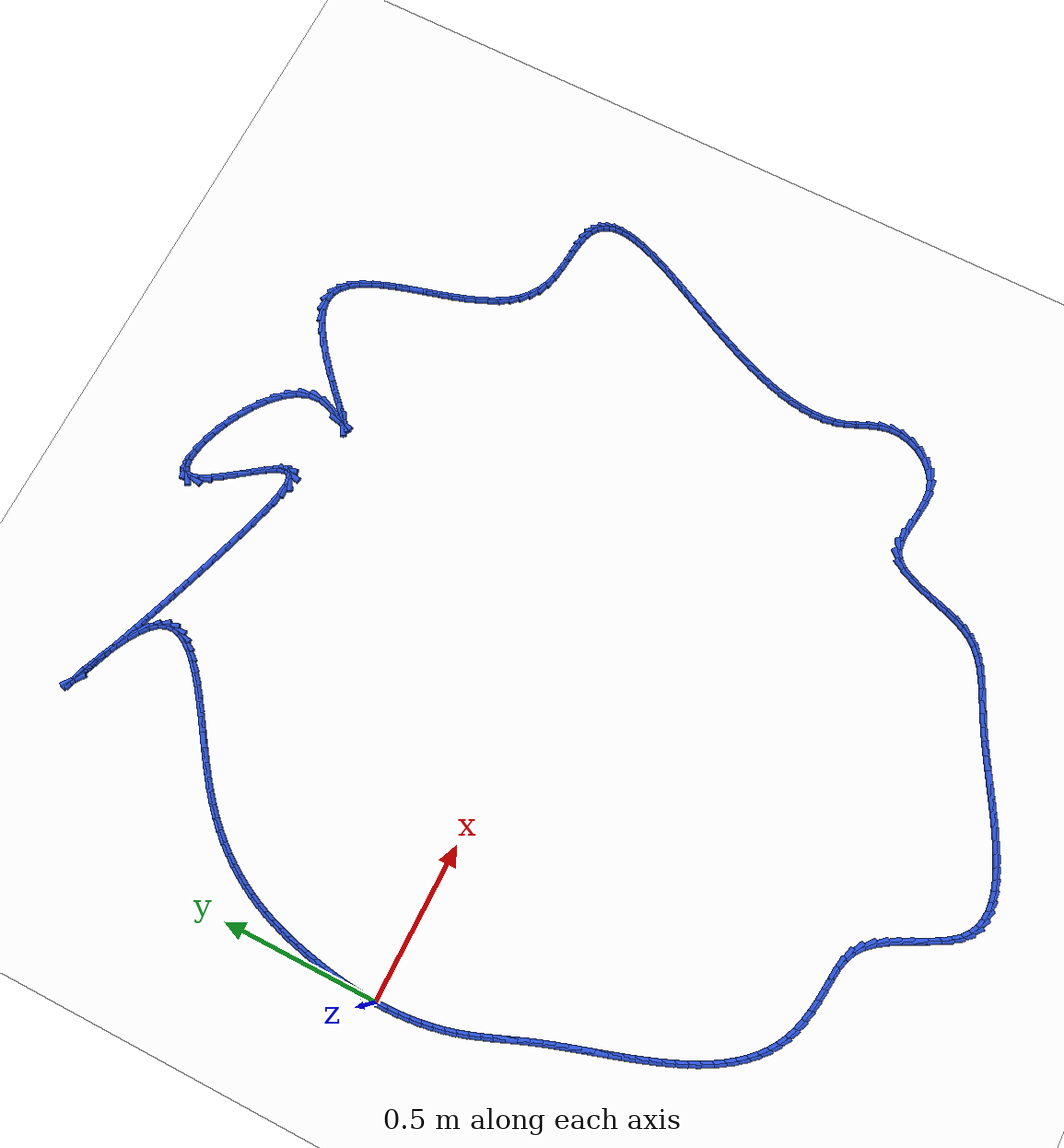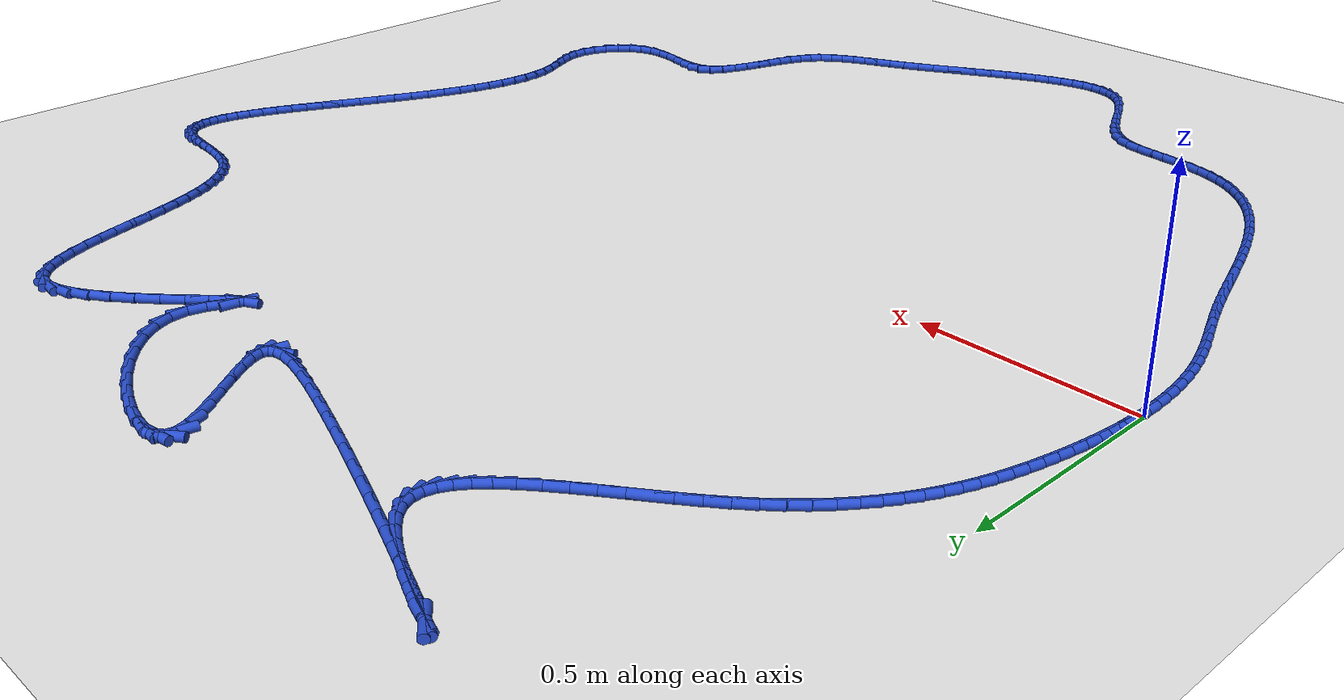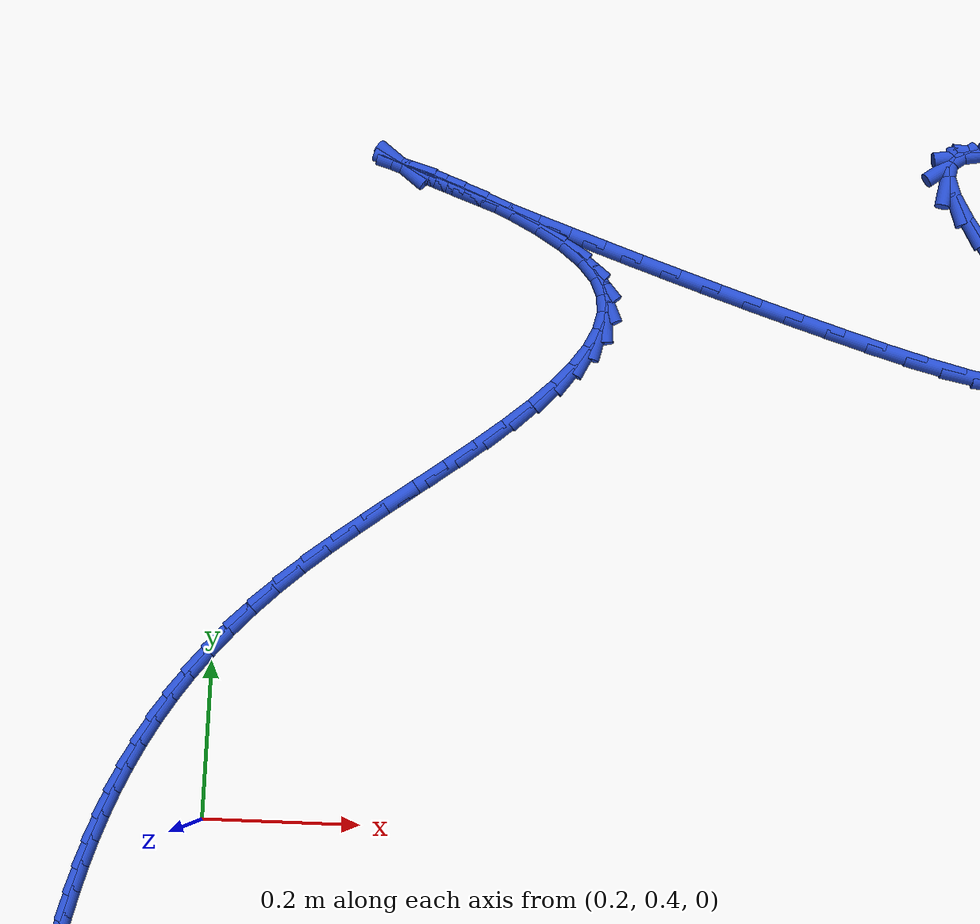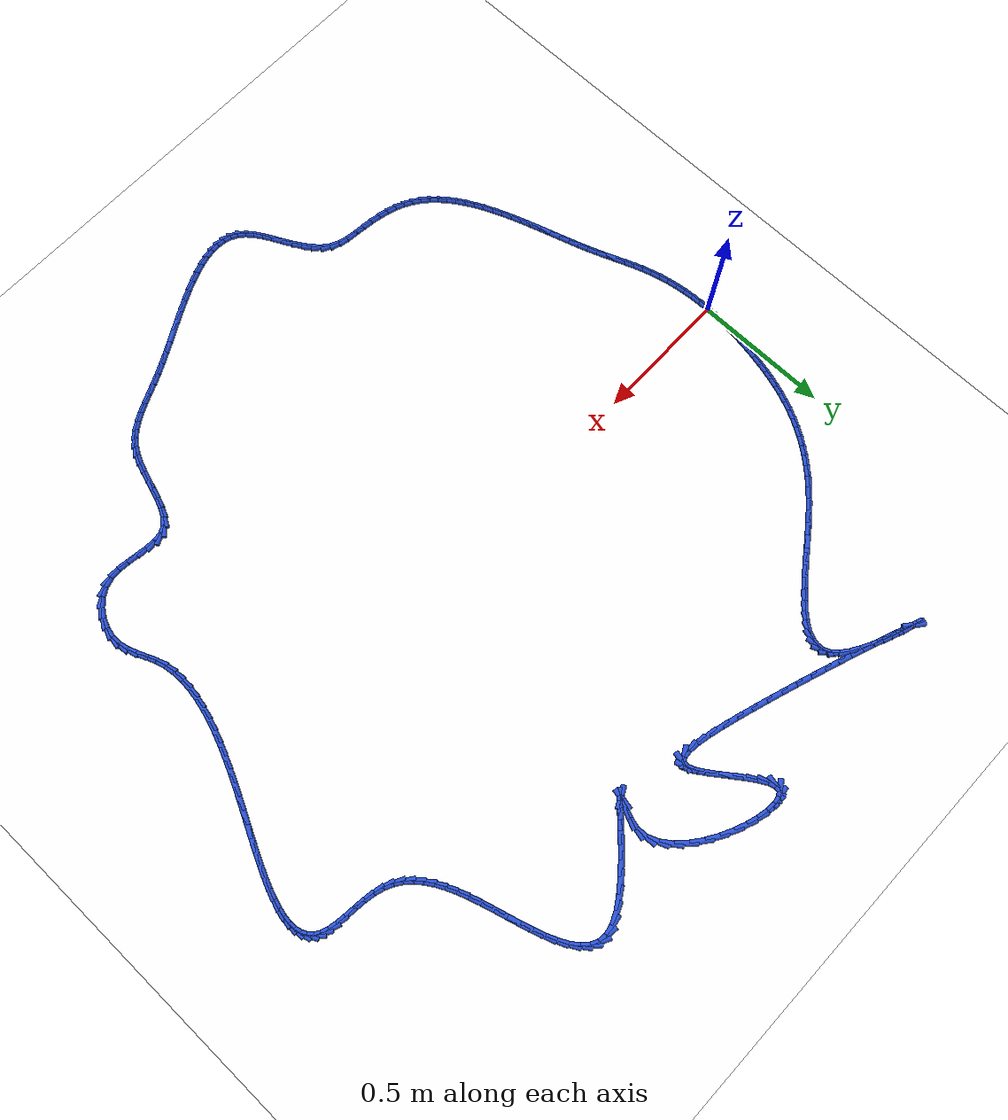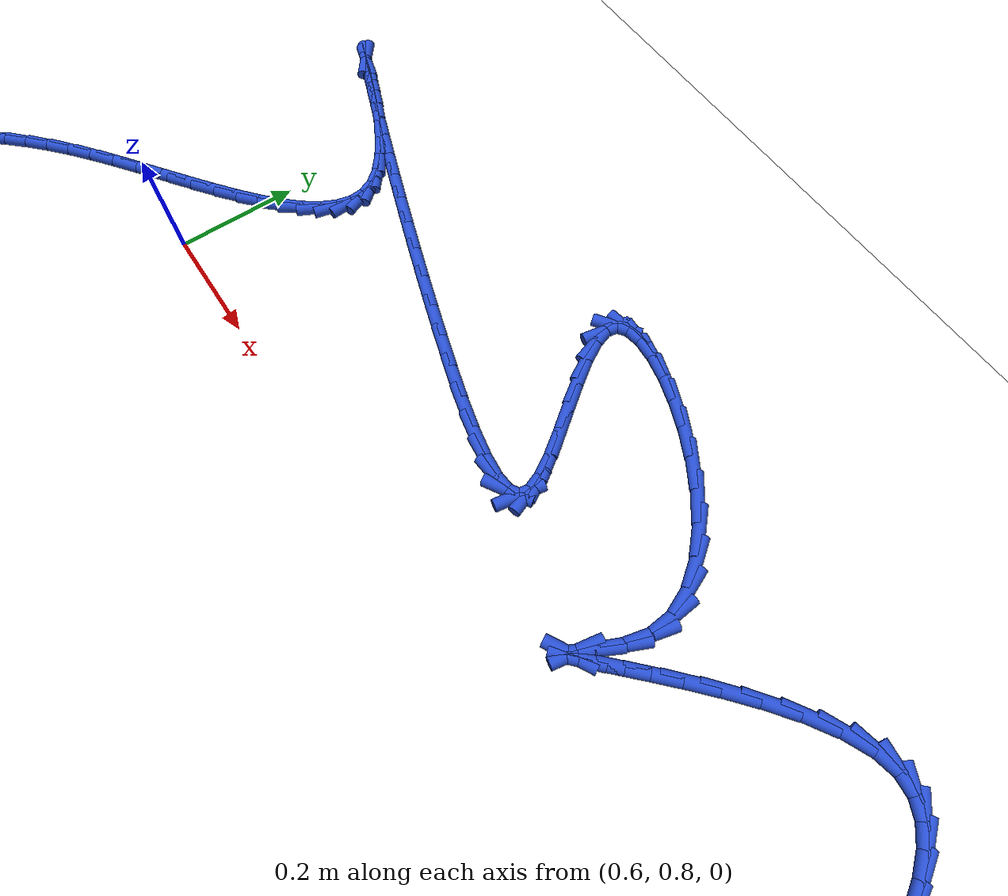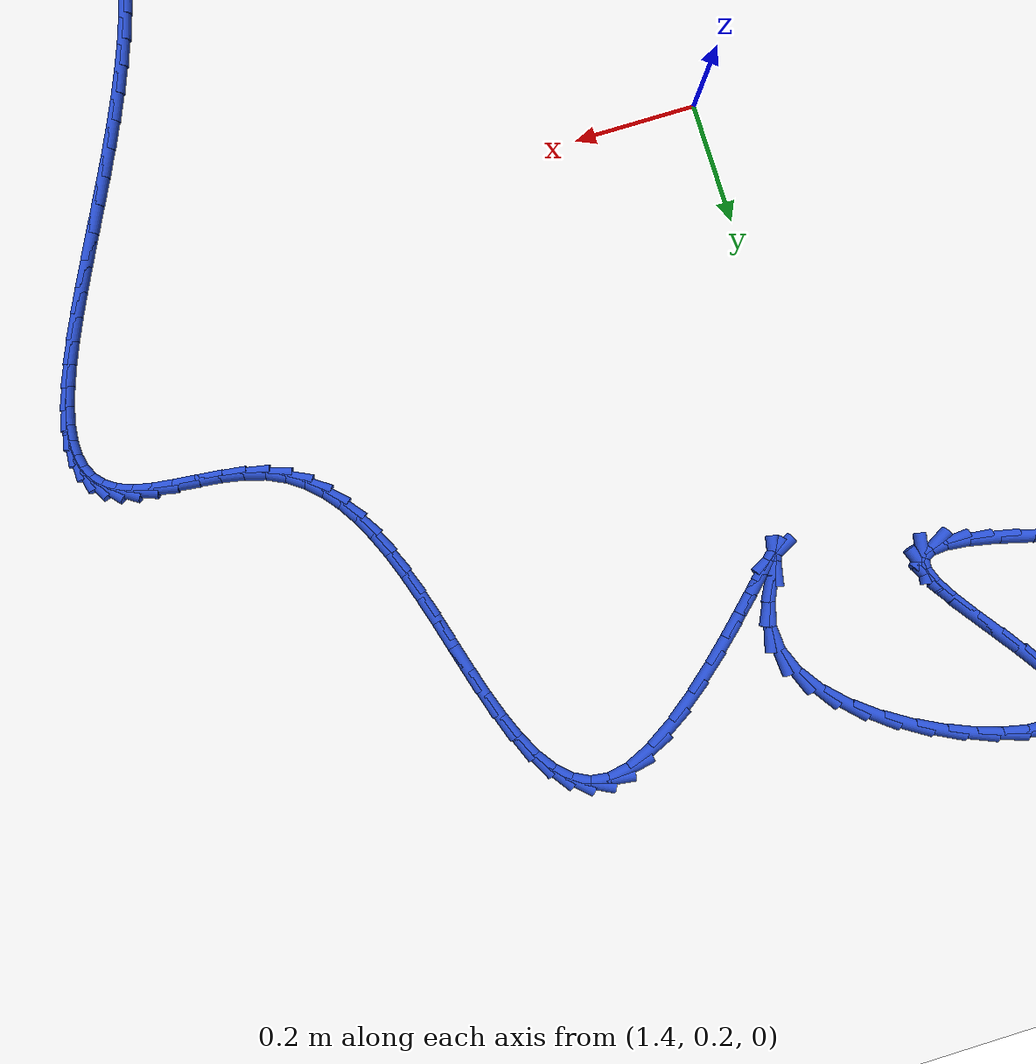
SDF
<sdf version="1.6">
 <world name="default">
  <light name="sun" type="directional">
   <pose>0 0 10 0 -0 0</pose>
   <diffuse>0.8 0.8 0.8 1</diffuse>
   <specular>0.2 0.2 0.2 1</specular>
   <attenuation>
    <range>1000</range>
    <constant>0.9</constant>
    <linear>0.01</linear>
    <quadratic>0.001</quadratic>
   </attenuation>
   <direction>-0.5 0.1 -0.9</direction>
  </light>
  <model name="ground_plane">
   <static>1</static>
   <link name="link">
    <collision name="collision">
     <geometry><plane><normal>0 0 1</normal><size>100 100</size></plane></geometry>
     <surface><friction><ode><mu>100</mu><mu2>50</mu2></ode></friction></surface>
    </collision>
    <visual name="visual">
     <cast_shadows>0</cast_shadows>
     <geometry><plane><normal>0 0 1</normal><size>100 100</size></plane></geometry>
     <material>
      <script><uri>file://media/materials/scripts/gazebo.material</uri><name>Gazebo/WhiteGlow</name></script>
     </material>
    </visual>
   </link>
  </model>
  <gravity>0 0 -9.8</gravity>
  <magnetic_field>6e-06 2.3e-05 -4.2e-05</magnetic_field>
  <atmosphere type="adiabatic"/>
  <physics name="default_physics" default="0" type="ode">
   <max_step_size>0.001</max_step_size>
   <real_time_factor>1</real_time_factor>
   <real_time_update_rate>1000</real_time_update_rate>
  </physics>
  <scene><ambient>0.4 0.4 0.4 1</ambient><background>0.7 0.7 0.7 1</background><shadows>1</shadows></scene>
  <spherical_coordinates>
   <surface_model>EARTH_WGS84</surface_model>
   <latitude_deg>0</latitude_deg>
   <longitude_deg>0</longitude_deg>
   <elevation>0</elevation>
   <heading_deg>0</heading_deg>
  </spherical_coordinates>
  <model name="line">
   <link name="link_0">
    <pose>-1.9081958235744878e-17 -4.163336342344337e-17 0.01 0 1.57 1.5376184945663542</pose>
    <collision name="collision">
     <geometry><cylinder><radius>0.01</radius><length>0.08</length></cylinder></geometry>
    </collision>
    <visual name="visual">
     <material>
      <script><name>Gazebo/Blue</name><uri>file://media/materials/scripts/gazebo.material</uri></script>
     </material>
     <geometry><cylinder><radius>0.01</radius><length>0.08</length></cylinder></geometry>
    </visual>
   </link>
   <link name="link_1">
    <pose>0.0011723475374481982 0.03532230004374317 0.01 0 1.57 1.5041014518438005</pose>
    <collision name="collision">
     <geometry><cylinder><radius>0.01</radius><length>0.08</length></cylinder></geometry>
    </collision>
    <visual name="visual">
     <material>
      <script><name>Gazebo/Blue</name><uri>file://media/materials/scripts/gazebo.material</uri></script>
     </material>
     <geometry><cylinder><radius>0.01</radius><length>0.08</length></cylinder></geometry>
    </visual>
   </link>
   <link name="link_2">
    <pose>0.003524206129973034 0.07053295716829418 0.01 0 1.57 1.4732190608263767</pose>
    <collision name="collision">
     <geometry><cylinder><radius>0.01</radius><length>0.08</length></cylinder></geometry>
    </collision>
    <visual name="visual">
     <material>
      <script><name>Gazebo/Blue</name><uri>file://media/materials/scripts/gazebo.material</uri></script>
     </material>
     <geometry><cylinder><radius>0.01</radius><length>0.08</length></cylinder></geometry>
    </visual>
   </link>
   <link name="link_3">
    <pose>0.0069527387851088555 0.10555796344591252 0.01 0 1.57 1.4448357763890065</pose>
    <collision name="collision">
     <geometry><cylinder><radius>0.01</radius><length>0.08</length></cylinder></geometry>
    </collision>
    <visual name="visual">
     <material>
      <script><name>Gazebo/Blue</name><uri>file://media/materials/scripts/gazebo.material</uri></script>
     </material>
     <geometry><cylinder><radius>0.01</radius><length>0.08</length></cylinder></geometry>
    </visual>
   </link>
   <link name="link_4">
    <pose>0.011355108510390009 0.14032331094885758 0.01 0 1.57 1.4188226467934741</pose>
    <collision name="collision">
     <geometry><cylinder><radius>0.01</radius><length>0.08</length></cylinder></geometry>
    </collision>
    <visual name="visual">
     <material>
      <script><name>Gazebo/Blue</name><uri>file://media/materials/scripts/gazebo.material</uri></script>
     </material>
     <geometry><cylinder><radius>0.01</radius><length>0.08</length></cylinder></geometry>
    </visual>
   </link>
   <link name="link_5">
    <pose>0.016628478313350854 0.17475499174938872 0.01 0 1.57 1.3950612516940333</pose>
    <collision name="collision">
     <geometry><cylinder><radius>0.01</radius><length>0.08</length></cylinder></geometry>
    </collision>
    <visual name="visual">
     <material>
      <script><name>Gazebo/Blue</name><uri>file://media/materials/scripts/gazebo.material</uri></script>
     </material>
     <geometry><cylinder><radius>0.01</radius><length>0.08</length></cylinder></geometry>
    </visual>
   </link>
   <link name="link_6">
    <pose>0.022670011201525744 0.2087789979197655 0.01 0 1.57 1.3734035935768434</pose>
    <collision name="collision">
     <geometry><cylinder><radius>0.01</radius><length>0.08</length></cylinder></geometry>
    </collision>
    <visual name="visual">
     <material>
      <script><name>Gazebo/Blue</name><uri>file://media/materials/scripts/gazebo.material</uri></script>
     </material>
     <geometry><cylinder><radius>0.01</radius><length>0.08</length></cylinder></geometry>
    </visual>
   </link>
   <link name="link_7">
    <pose>0.029378520613141793 0.2423220380094555 0.01 0 1.57 1.3514736060687444</pose>
    <collision name="collision">
     <geometry><cylinder><radius>0.01</radius><length>0.08</length></cylinder></geometry>
    </collision>
    <visual name="visual">
     <material>
      <script><name>Gazebo/Blue</name><uri>file://media/materials/scripts/gazebo.material</uri></script>
     </material>
     <geometry><cylinder><radius>0.01</radius><length>0.08</length></cylinder></geometry>
    </visual>
   </link>
   <link name="link_8">
    <pose>0.036740479377144475 0.27534887485025 0.01 0 1.57 1.3258562833953265</pose>
    <collision name="collision">
     <geometry><cylinder><radius>0.01</radius><length>0.08</length></cylinder></geometry>
    </collision>
    <visual name="visual">
     <material>
      <script><name>Gazebo/Blue</name><uri>file://media/materials/scripts/gazebo.material</uri></script>
     </material>
     <geometry><cylinder><radius>0.01</radius><length>0.08</length></cylinder></geometry>
    </visual>
   </link>
   <link name="link_9">
    <pose>0.044872070949275145 0.3078805806410485 0.01 0 1.57 1.296328765569726</pose>
    <collision name="collision">
     <geometry><cylinder><radius>0.01</radius><length>0.08</length></cylinder></geometry>
    </collision>
    <visual name="visual">
     <material>
      <script><name>Gazebo/Blue</name><uri>file://media/materials/scripts/gazebo.material</uri></script>
     </material>
     <geometry><cylinder><radius>0.01</radius><length>0.08</length></cylinder></geometry>
    </visual>
   </link>
   <link name="link_10">
    <pose>0.053899946386491066 0.339942771726548 0.01 0 1.57 1.2630180009428806</pose>
    <collision name="collision">
     <geometry><cylinder><radius>0.01</radius><length>0.08</length></cylinder></geometry>
    </collision>
    <visual name="visual">
     <material>
      <script><name>Gazebo/Blue</name><uri>file://media/materials/scripts/gazebo.material</uri></script>
     </material>
     <geometry><cylinder><radius>0.01</radius><length>0.08</length></cylinder></geometry>
    </visual>
   </link>
   <link name="link_11">
    <pose>0.06395075674574952 0.3715610644514454 0.01 0 1.57 1.2261378673215297</pose>
    <collision name="collision">
     <geometry><cylinder><radius>0.01</radius><length>0.08</length></cylinder></geometry>
    </collision>
    <visual name="visual">
     <material>
      <script><name>Gazebo/Blue</name><uri>file://media/materials/scripts/gazebo.material</uri></script>
     </material>
     <geometry><cylinder><radius>0.01</radius><length>0.08</length></cylinder></geometry>
    </visual>
   </link>
   <link name="link_12">
    <pose>0.07515115308400772 0.40276107516043713 0.01 0 1.57 1.185996569558987</pose>
    <collision name="collision">
     <geometry><cylinder><radius>0.01</radius><length>0.08</length></cylinder></geometry>
    </collision>
    <visual name="visual">
     <material>
      <script><name>Gazebo/Blue</name><uri>file://media/materials/scripts/gazebo.material</uri></script>
     </material>
     <geometry><cylinder><radius>0.01</radius><length>0.08</length></cylinder></geometry>
    </visual>
   </link>
   <link name="link_13">
    <pose>0.08762778645822293 0.4335684201982204 0.01 0 1.57 1.142998102521094</pose>
    <collision name="collision">
     <geometry><cylinder><radius>0.01</radius><length>0.08</length></cylinder></geometry>
    </collision>
    <visual name="visual">
     <material>
      <script><name>Gazebo/Blue</name><uri>file://media/materials/scripts/gazebo.material</uri></script>
     </material>
     <geometry><cylinder><radius>0.01</radius><length>0.08</length></cylinder></geometry>
    </visual>
   </link>
   <link name="link_14">
    <pose>0.10150730792535245 0.464008715909492 0.01 0 1.57 1.0976358573032878</pose>
    <collision name="collision">
     <geometry><cylinder><radius>0.01</radius><length>0.08</length></cylinder></geometry>
    </collision>
    <visual name="visual">
     <material>
      <script><name>Gazebo/Blue</name><uri>file://media/materials/scripts/gazebo.material</uri></script>
     </material>
     <geometry><cylinder><radius>0.01</radius><length>0.08</length></cylinder></geometry>
    </visual>
   </link>
   <link name="link_15">
    <pose>0.11691636854235349 0.4941075786389486 0.01 0 1.57 1.0504773841870771</pose>
    <collision name="collision">
     <geometry><cylinder><radius>0.01</radius><length>0.08</length></cylinder></geometry>
    </collision>
    <visual name="visual">
     <material>
      <script><name>Gazebo/Blue</name><uri>file://media/materials/scripts/gazebo.material</uri></script>
     </material>
     <geometry><cylinder><radius>0.01</radius><length>0.08</length></cylinder></geometry>
    </visual>
   </link>
   <link name="link_16">
    <pose>0.13398161936618333 0.5238906247312872 0.01 0 1.57 1.0021407896355405</pose>
    <collision name="collision">
     <geometry><cylinder><radius>0.01</radius><length>0.08</length></cylinder></geometry>
    </collision>
    <visual name="visual">
     <material>
      <script><name>Gazebo/Blue</name><uri>file://media/materials/scripts/gazebo.material</uri></script>
     </material>
     <geometry><cylinder><radius>0.01</radius><length>0.08</length></cylinder></geometry>
    </visual>
   </link>
   <link name="link_17">
    <pose>0.15282971145379923 0.5533834705312044 0.01 0 1.57 0.9532649181700665</pose>
    <collision name="collision">
     <geometry><cylinder><radius>0.01</radius><length>0.08</length></cylinder></geometry>
    </collision>
    <visual name="visual">
     <material>
      <script><name>Gazebo/Blue</name><uri>file://media/materials/scripts/gazebo.material</uri></script>
     </material>
     <geometry><cylinder><radius>0.01</radius><length>0.08</length></cylinder></geometry>
    </visual>
   </link>
   <link name="link_18">
    <pose>0.17358729586215832 0.5826117323833971 0.01 0 1.57 0.9044768626946498</pose>
    <collision name="collision">
     <geometry><cylinder><radius>0.01</radius><length>0.08</length></cylinder></geometry>
    </collision>
    <visual name="visual">
     <material>
      <script><name>Gazebo/Blue</name><uri>file://media/materials/scripts/gazebo.material</uri></script>
     </material>
     <geometry><cylinder><radius>0.01</radius><length>0.08</length></cylinder></geometry>
    </visual>
   </link>
   <link name="link_19">
    <pose>0.19638102364821808 0.6116010266325624 0.01 0 1.57 0.8563609867290765</pose>
    <collision name="collision">
     <geometry><cylinder><radius>0.01</radius><length>0.08</length></cylinder></geometry>
    </collision>
    <visual name="visual">
     <material>
      <script><name>Gazebo/Blue</name><uri>file://media/materials/scripts/gazebo.material</uri></script>
     </material>
     <geometry><cylinder><radius>0.01</radius><length>0.08</length></cylinder></geometry>
    </visual>
   </link>
   <link name="link_20">
    <pose>0.22133754586893561 0.640376969623397 0.01 0 1.57 0.8094332972684989</pose>
    <collision name="collision">
     <geometry><cylinder><radius>0.01</radius><length>0.08</length></cylinder></geometry>
    </collision>
    <visual name="visual">
     <material>
      <script><name>Gazebo/Blue</name><uri>file://media/materials/scripts/gazebo.material</uri></script>
     </material>
     <geometry><cylinder><radius>0.01</radius><length>0.08</length></cylinder></geometry>
    </visual>
   </link>
   <link name="link_21">
    <pose>0.2485835135812682 0.6689651777005974 0.01 0 1.57 0.7641238036510345</pose>
    <collision name="collision">
     <geometry><cylinder><radius>0.01</radius><length>0.08</length></cylinder></geometry>
    </collision>
    <visual name="visual">
     <material>
      <script><name>Gazebo/Blue</name><uri>file://media/materials/scripts/gazebo.material</uri></script>
     </material>
     <geometry><cylinder><radius>0.01</radius><length>0.08</length></cylinder></geometry>
    </visual>
   </link>
   <link name="link_22">
    <pose>0.27824557784217324 0.6973912672088609 0.01 0 1.57 0.7207678551243164</pose>
    <collision name="collision">
     <geometry><cylinder><radius>0.01</radius><length>0.08</length></cylinder></geometry>
    </collision>
    <visual name="visual">
     <material>
      <script><name>Gazebo/Blue</name><uri>file://media/materials/scripts/gazebo.material</uri></script>
     </material>
     <geometry><cylinder><radius>0.01</radius><length>0.08</length></cylinder></geometry>
    </visual>
   </link>
   <link name="link_23">
    <pose>0.3104503897086077 0.725680854492884 0.01 0 1.57 0.6811791569323755</pose>
    <collision name="collision">
     <geometry><cylinder><radius>0.01</radius><length>0.08</length></cylinder></geometry>
    </collision>
    <visual name="visual">
     <material>
      <script><name>Gazebo/Blue</name><uri>file://media/materials/scripts/gazebo.material</uri></script>
     </material>
     <geometry><cylinder><radius>0.01</radius><length>0.08</length></cylinder></geometry>
    </visual>
   </link>
   <link name="link_24">
    <pose>0.3452029569986167 0.7538517541515303 0.01 0 1.57 0.6522928884079793</pose>
    <collision name="collision">
     <geometry><cylinder><radius>0.01</radius><length>0.08</length></cylinder></geometry>
    </collision>
    <visual name="visual">
     <material>
      <script><name>Gazebo/Blue</name><uri>file://media/materials/scripts/gazebo.material</uri></script>
     </material>
     <geometry><cylinder><radius>0.01</radius><length>0.08</length></cylinder></geometry>
    </visual>
   </link>
   <link name="link_25">
    <pose>0.38190108450779225 0.7818828370355952 0.01 0 1.57 0.6344573457232812</pose>
    <collision name="collision">
     <geometry><cylinder><radius>0.01</radius><length>0.08</length></cylinder></geometry>
    </collision>
    <visual name="visual">
     <material>
      <script><name>Gazebo/Blue</name><uri>file://media/materials/scripts/gazebo.material</uri></script>
     </material>
     <geometry><cylinder><radius>0.01</radius><length>0.08</length></cylinder></geometry>
    </visual>
   </link>
   <link name="link_26">
    <pose>0.4197534960639988 0.8097408470444268 0.01 0 1.57 0.6263735013264908</pose>
    <collision name="collision">
     <geometry><cylinder><radius>0.01</radius><length>0.08</length></cylinder></geometry>
    </collision>
    <visual name="visual">
     <material>
      <script><name>Gazebo/Blue</name><uri>file://media/materials/scripts/gazebo.material</uri></script>
     </material>
     <geometry><cylinder><radius>0.01</radius><length>0.08</length></cylinder></geometry>
    </visual>
   </link>
   <link name="link_27">
    <pose>0.4579688545080371 0.83739252416589 0.01 0 1.57 0.6275949090159018</pose>
    <collision name="collision">
     <geometry><cylinder><radius>0.01</radius><length>0.08</length></cylinder></geometry>
    </collision>
    <visual name="visual">
     <material>
      <script><name>Gazebo/Blue</name><uri>file://media/materials/scripts/gazebo.material</uri></script>
     </material>
     <geometry><cylinder><radius>0.01</radius><length>0.08</length></cylinder></geometry>
    </visual>
   </link>
   <link name="link_28">
    <pose>0.49575582268070717 0.8648046083878488 0.01 0 1.57 0.6384732017835405</pose>
    <collision name="collision">
     <geometry><cylinder><radius>0.01</radius><length>0.08</length></cylinder></geometry>
    </collision>
    <visual name="visual">
     <material>
      <script><name>Gazebo/Blue</name><uri>file://media/materials/scripts/gazebo.material</uri></script>
     </material>
     <geometry><cylinder><radius>0.01</radius><length>0.08</length></cylinder></geometry>
    </visual>
   </link>
   <link name="link_29">
    <pose>0.5323230634228094 0.8919438396981678 0.01 0 1.57 0.6602509918935555</pose>
    <collision name="collision">
     <geometry><cylinder><radius>0.01</radius><length>0.08</length></cylinder></geometry>
    </collision>
    <visual name="visual">
     <material>
      <script><name>Gazebo/Blue</name><uri>file://media/materials/scripts/gazebo.material</uri></script>
     </material>
     <geometry><cylinder><radius>0.01</radius><length>0.08</length></cylinder></geometry>
    </visual>
   </link>
   <link name="link_30">
    <pose>0.5668792395751441 0.9187769580847116 0.01 0 1.57 0.695337675064765</pose>
    <collision name="collision">
     <geometry><cylinder><radius>0.01</radius><length>0.08</length></cylinder></geometry>
    </collision>
    <visual name="visual">
     <material>
      <script><name>Gazebo/Blue</name><uri>file://media/materials/scripts/gazebo.material</uri></script>
     </material>
     <geometry><cylinder><radius>0.01</radius><length>0.08</length></cylinder></geometry>
    </visual>
   </link>
   <link name="link_31">
    <pose>0.5986330139785113 0.9452707035353441 0.01 0 1.57 0.7478535469513538</pose>
    <collision name="collision">
     <geometry><cylinder><radius>0.01</radius><length>0.08</length></cylinder></geometry>
    </collision>
    <visual name="visual">
     <material>
      <script><name>Gazebo/Blue</name><uri>file://media/materials/scripts/gazebo.material</uri></script>
     </material>
     <geometry><cylinder><radius>0.01</radius><length>0.08</length></cylinder></geometry>
    </visual>
   </link>
   <link name="link_32">
    <pose>0.6267930494737115 0.9713918160379302 0.01 0 1.57 0.8245830480036059</pose>
    <collision name="collision">
     <geometry><cylinder><radius>0.01</radius><length>0.08</length></cylinder></geometry>
    </collision>
    <visual name="visual">
     <material>
      <script><name>Gazebo/Blue</name><uri>file://media/materials/scripts/gazebo.material</uri></script>
     </material>
     <geometry><cylinder><radius>0.01</radius><length>0.08</length></cylinder></geometry>
    </visual>
   </link>
   <link name="link_33">
    <pose>0.6505680089015451 0.9971070355803344 0.01 0 1.57 0.9364346434123867</pose>
    <collision name="collision">
     <geometry><cylinder><radius>0.01</radius><length>0.08</length></cylinder></geometry>
    </collision>
    <visual name="visual">
     <material>
      <script><name>Gazebo/Blue</name><uri>file://media/materials/scripts/gazebo.material</uri></script>
     </material>
     <geometry><cylinder><radius>0.01</radius><length>0.08</length></cylinder></geometry>
    </visual>
   </link>
   <link name="link_34">
    <pose>0.6691665551028121 1.022383102150421 0.01 0 1.57 1.0997910098991046</pose>
    <collision name="collision">
     <geometry><cylinder><radius>0.01</radius><length>0.08</length></cylinder></geometry>
    </collision>
    <visual name="visual">
     <material>
      <script><name>Gazebo/Blue</name><uri>file://media/materials/scripts/gazebo.material</uri></script>
     </material>
     <geometry><cylinder><radius>0.01</radius><length>0.08</length></cylinder></geometry>
    </visual>
   </link>
   <link name="link_35">
    <pose>0.6817973509183131 1.0471867557360544 0.01 0 1.57 1.3336878575902162</pose>
    <collision name="collision">
     <geometry><cylinder><radius>0.01</radius><length>0.08</length></cylinder></geometry>
    </collision>
    <visual name="visual">
     <material>
      <script><name>Gazebo/Blue</name><uri>file://media/materials/scripts/gazebo.material</uri></script>
     </material>
     <geometry><cylinder><radius>0.01</radius><length>0.08</length></cylinder></geometry>
    </visual>
   </link>
   <link name="link_36">
    <pose>0.687669059188848 1.0714847363250992 0.01 0 1.57 -1.5002576724214727</pose>
    <collision name="collision">
     <geometry><cylinder><radius>0.01</radius><length>0.08</length></cylinder></geometry>
    </collision>
    <visual name="visual">
     <material>
      <script><name>Gazebo/Blue</name><uri>file://media/materials/scripts/gazebo.material</uri></script>
     </material>
     <geometry><cylinder><radius>0.01</radius><length>0.08</length></cylinder></geometry>
    </visual>
   </link>
   <link name="link_37">
    <pose>0.6859903427552174 1.0952437839054197 0.01 0 1.57 -1.1628750432676997</pose>
    <collision name="collision">
     <geometry><cylinder><radius>0.01</radius><length>0.08</length></cylinder></geometry>
    </collision>
    <visual name="visual">
     <material>
      <script><name>Gazebo/Blue</name><uri>file://media/materials/scripts/gazebo.material</uri></script>
     </material>
     <geometry><cylinder><radius>0.01</radius><length>0.08</length></cylinder></geometry>
    </visual>
   </link>
   <link name="link_38">
    <pose>0.6759698644582215 1.1184306384648806 0.01 0 1.57 -0.8698642629103456</pose>
    <collision name="collision">
     <geometry><cylinder><radius>0.01</radius><length>0.08</length></cylinder></geometry>
    </collision>
    <visual name="visual">
     <material>
      <script><name>Gazebo/Blue</name><uri>file://media/materials/scripts/gazebo.material</uri></script>
     </material>
     <geometry><cylinder><radius>0.01</radius><length>0.08</length></cylinder></geometry>
    </visual>
   </link>
   <link name="link_39">
    <pose>0.6569234554801319 1.1410006038826874 0.01 0 1.57 -0.6767150941291953</pose>
    <collision name="collision">
     <geometry><cylinder><radius>0.01</radius><length>0.08</length></cylinder></geometry>
    </collision>
    <visual name="visual">
     <material>
      <script><name>Gazebo/Blue</name><uri>file://media/materials/scripts/gazebo.material</uri></script>
     </material>
     <geometry><cylinder><radius>0.01</radius><length>0.08</length></cylinder></geometry>
    </visual>
   </link>
   <link name="link_40">
    <pose>0.6298755230438031 1.1627266590997027 0.01 0 1.57 -0.5608009420195447</pose>
    <collision name="collision">
     <geometry><cylinder><radius>0.01</radius><length>0.08</length></cylinder></geometry>
    </collision>
    <visual name="visual">
     <material>
      <script><name>Gazebo/Blue</name><uri>file://media/materials/scripts/gazebo.material</uri></script>
     </material>
     <geometry><cylinder><radius>0.01</radius><length>0.08</length></cylinder></geometry>
    </visual>
   </link>
   <link name="link_41">
    <pose>0.597221610318199 1.1832354669017593 0.01 0 1.57 -0.48575509200364586</pose>
    <collision name="collision">
     <geometry><cylinder><radius>0.01</radius><length>0.08</length></cylinder></geometry>
    </collision>
    <visual name="visual">
     <material>
      <script><name>Gazebo/Blue</name><uri>file://media/materials/scripts/gazebo.material</uri></script>
     </material>
     <geometry><cylinder><radius>0.01</radius><length>0.08</length></cylinder></geometry>
    </visual>
   </link>
   <link name="link_42">
    <pose>0.5613959150001723 1.202149565186918 0.01 0 1.57 -0.43390760819317675</pose>
    <collision name="collision">
     <geometry><cylinder><radius>0.01</radius><length>0.08</length></cylinder></geometry>
    </collision>
    <visual name="visual">
     <material>
      <script><name>Gazebo/Blue</name><uri>file://media/materials/scripts/gazebo.material</uri></script>
     </material>
     <geometry><cylinder><radius>0.01</radius><length>0.08</length></cylinder></geometry>
    </visual>
   </link>
   <link name="link_43">
    <pose>0.5248326347865754 1.2190914918532414 0.01 0 1.57 -0.396366696308613</pose>
    <collision name="collision">
     <geometry><cylinder><radius>0.01</radius><length>0.08</length></cylinder></geometry>
    </collision>
    <visual name="visual">
     <material>
      <script><name>Gazebo/Blue</name><uri>file://media/materials/scripts/gazebo.material</uri></script>
     </material>
     <geometry><cylinder><radius>0.01</radius><length>0.08</length></cylinder></geometry>
    </visual>
   </link>
   <link name="link_44">
    <pose>0.48996596737426173 1.2336837847987914 0.01 0 1.57 -0.3684122027156938</pose>
    <collision name="collision">
     <geometry><cylinder><radius>0.01</radius><length>0.08</length></cylinder></geometry>
    </collision>
    <visual name="visual">
     <material>
      <script><name>Gazebo/Blue</name><uri>file://media/materials/scripts/gazebo.material</uri></script>
     </material>
     <geometry><cylinder><radius>0.01</radius><length>0.08</length></cylinder></geometry>
    </visual>
   </link>
   <link name="link_45">
    <pose>0.459230110460084 1.2455489819216297 0.01 0 1.57 -0.3477196889810161</pose>
    <collision name="collision">
     <geometry><cylinder><radius>0.01</radius><length>0.08</length></cylinder></geometry>
    </collision>
    <visual name="visual">
     <material>
      <script><name>Gazebo/Blue</name><uri>file://media/materials/scripts/gazebo.material</uri></script>
     </material>
     <geometry><cylinder><radius>0.01</radius><length>0.08</length></cylinder></geometry>
    </visual>
   </link>
   <link name="link_46">
    <pose>0.43505926174089526 1.254309621119818 0.01 0 1.57 -0.3317245176585386</pose>
    <collision name="collision">
     <geometry><cylinder><radius>0.01</radius><length>0.08</length></cylinder></geometry>
    </collision>
    <visual name="visual">
     <material>
      <script><name>Gazebo/Blue</name><uri>file://media/materials/scripts/gazebo.material</uri></script>
     </material>
     <geometry><cylinder><radius>0.01</radius><length>0.08</length></cylinder></geometry>
    </visual>
   </link>
   <link name="link_47">
    <pose>0.4195041189200679 1.2596676344279971 0.01 0 1.57 -0.2922968607897403</pose>
    <collision name="collision">
     <geometry><cylinder><radius>0.01</radius><length>0.08</length></cylinder></geometry>
    </collision>
    <visual name="visual">
     <material>
      <script><name>Gazebo/Blue</name><uri>file://media/materials/scripts/gazebo.material</uri></script>
     </material>
     <geometry><cylinder><radius>0.01</radius><length>0.08</length></cylinder></geometry>
    </visual>
   </link>
   <link name="link_48">
    <pose>0.41263201039878766 1.2617355611713998 0.01 0 1.57 -0.6678579510635081</pose>
    <collision name="collision">
     <geometry><cylinder><radius>0.01</radius><length>0.08</length></cylinder></geometry>
    </collision>
    <visual name="visual">
     <material>
      <script><name>Gazebo/Blue</name><uri>file://media/materials/scripts/gazebo.material</uri></script>
     </material>
     <geometry><cylinder><radius>0.01</radius><length>0.08</length></cylinder></geometry>
    </visual>
   </link>
   <link name="link_49">
    <pose>0.41387099046970427 1.260758286481638 0.01 0 1.57 -0.4063929415647524</pose>
    <collision name="collision">
     <geometry><cylinder><radius>0.01</radius><length>0.08</length></cylinder></geometry>
    </collision>
    <visual name="visual">
     <material>
      <script><name>Gazebo/Blue</name><uri>file://media/materials/scripts/gazebo.material</uri></script>
     </material>
     <geometry><cylinder><radius>0.01</radius><length>0.08</length></cylinder></geometry>
    </visual>
   </link>
   <link name="link_50">
    <pose>0.42264880263206767 1.2569807598323701 0.01 0 1.57 -0.38242534598650335</pose>
    <collision name="collision">
     <geometry><cylinder><radius>0.01</radius><length>0.08</length></cylinder></geometry>
    </collision>
    <visual name="visual">
     <material>
      <script><name>Gazebo/Blue</name><uri>file://media/materials/scripts/gazebo.material</uri></script>
     </material>
     <geometry><cylinder><radius>0.01</radius><length>0.08</length></cylinder></geometry>
    </visual>
   </link>
   <link name="link_51">
    <pose>0.4383931903851278 1.2506479306972547 0.01 0 1.57 -0.3722122729546029</pose>
    <collision name="collision">
     <geometry><cylinder><radius>0.01</radius><length>0.08</length></cylinder></geometry>
    </collision>
    <visual name="visual">
     <material>
      <script><name>Gazebo/Blue</name><uri>file://media/materials/scripts/gazebo.material</uri></script>
     </material>
     <geometry><cylinder><radius>0.01</radius><length>0.08</length></cylinder></geometry>
    </visual>
   </link>
   <link name="link_52">
    <pose>0.4605318972281346 1.2420047485499477 0.01 0 1.57 -0.36575372331158235</pose>
    <collision name="collision">
     <geometry><cylinder><radius>0.01</radius><length>0.08</length></cylinder></geometry>
    </collision>
    <visual name="visual">
     <material>
      <script><name>Gazebo/Blue</name><uri>file://media/materials/scripts/gazebo.material</uri></script>
     </material>
     <geometry><cylinder><radius>0.01</radius><length>0.08</length></cylinder></geometry>
    </visual>
   </link>
   <link name="link_53">
    <pose>0.48849266666033836 1.231296162864109 0.01 0 1.57 -0.36075104170725936</pose>
    <collision name="collision">
     <geometry><cylinder><radius>0.01</radius><length>0.08</length></cylinder></geometry>
    </collision>
    <visual name="visual">
     <material>
      <script><name>Gazebo/Blue</name><uri>file://media/materials/scripts/gazebo.material</uri></script>
     </material>
     <geometry><cylinder><radius>0.01</radius><length>0.08</length></cylinder></geometry>
    </visual>
   </link>
   <link name="link_54">
    <pose>0.5217032421809886 1.2187671231133954 0.01 0 1.57 -0.35637352396076943</pose>
    <collision name="collision">
     <geometry><cylinder><radius>0.01</radius><length>0.08</length></cylinder></geometry>
    </collision>
    <visual name="visual">
     <material>
      <script><name>Gazebo/Blue</name><uri>file://media/materials/scripts/gazebo.material</uri></script>
     </material>
     <geometry><cylinder><radius>0.01</radius><length>0.08</length></cylinder></geometry>
    </visual>
   </link>
   <link name="link_55">
    <pose>0.5595913672893355 1.2046625787714647 0.01 0 1.57 -0.35223200185662357</pose>
    <collision name="collision">
     <geometry><cylinder><radius>0.01</radius><length>0.08</length></cylinder></geometry>
    </collision>
    <visual name="visual">
     <material>
      <script><name>Gazebo/Blue</name><uri>file://media/materials/scripts/gazebo.material</uri></script>
     </material>
     <geometry><cylinder><radius>0.01</radius><length>0.08</length></cylinder></geometry>
    </visual>
   </link>
   <link name="link_56">
    <pose>0.6015847854846289 1.1892274793119748 0.01 0 1.57 -0.3481040775110137</pose>
    <collision name="collision">
     <geometry><cylinder><radius>0.01</radius><length>0.08</length></cylinder></geometry>
    </collision>
    <visual name="visual">
     <material>
      <script><name>Gazebo/Blue</name><uri>file://media/materials/scripts/gazebo.material</uri></script>
     </material>
     <geometry><cylinder><radius>0.01</radius><length>0.08</length></cylinder></geometry>
    </visual>
   </link>
   <link name="link_57">
    <pose>0.6471112402661185 1.172706774208584 0.01 0 1.57 -0.34383749907045763</pose>
    <collision name="collision">
     <geometry><cylinder><radius>0.01</radius><length>0.08</length></cylinder></geometry>
    </collision>
    <visual name="visual">
     <material>
      <script><name>Gazebo/Blue</name><uri>file://media/materials/scripts/gazebo.material</uri></script>
     </material>
     <geometry><cylinder><radius>0.01</radius><length>0.08</length></cylinder></geometry>
    </visual>
   </link>
   <link name="link_58">
    <pose>0.6955984751330551 1.1553454129349492 0.01 0 1.57 -0.339308658354717</pose>
    <collision name="collision">
     <geometry><cylinder><radius>0.01</radius><length>0.08</length></cylinder></geometry>
    </collision>
    <visual name="visual">
     <material>
      <script><name>Gazebo/Blue</name><uri>file://media/materials/scripts/gazebo.material</uri></script>
     </material>
     <geometry><cylinder><radius>0.01</radius><length>0.08</length></cylinder></geometry>
    </visual>
   </link>
   <link name="link_59">
    <pose>0.7464742335846878 1.1373883449647288 0.01 0 1.57 -0.3344009776181328</pose>
    <collision name="collision">
     <geometry><cylinder><radius>0.01</radius><length>0.08</length></cylinder></geometry>
    </collision>
    <visual name="visual">
     <material>
      <script><name>Gazebo/Blue</name><uri>file://media/materials/scripts/gazebo.material</uri></script>
     </material>
     <geometry><cylinder><radius>0.01</radius><length>0.08</length></cylinder></geometry>
    </visual>
   </link>
   <link name="link_60">
    <pose>0.799166259120267 1.1190805197715805 0.01 0 1.57 -0.3289907458326644</pose>
    <collision name="collision">
     <geometry><cylinder><radius>0.01</radius><length>0.08</length></cylinder></geometry>
    </collision>
    <visual name="visual">
     <material>
      <script><name>Gazebo/Blue</name><uri>file://media/materials/scripts/gazebo.material</uri></script>
     </material>
     <geometry><cylinder><radius>0.01</radius><length>0.08</length></cylinder></geometry>
    </visual>
   </link>
   <link name="link_61">
    <pose>0.8531022952390424 1.1006668868291625 0.01 0 1.57 -0.32293499088508726</pose>
    <collision name="collision">
     <geometry><cylinder><radius>0.01</radius><length>0.08</length></cylinder></geometry>
    </collision>
    <visual name="visual">
     <material>
      <script><name>Gazebo/Blue</name><uri>file://media/materials/scripts/gazebo.material</uri></script>
     </material>
     <geometry><cylinder><radius>0.01</radius><length>0.08</length></cylinder></geometry>
    </visual>
   </link>
   <link name="link_62">
    <pose>0.907710085440264 1.082392395611132 0.01 0 1.57 -0.3160582097542931</pose>
    <collision name="collision">
     <geometry><cylinder><radius>0.01</radius><length>0.08</length></cylinder></geometry>
    </collision>
    <visual name="visual">
     <material>
      <script><name>Gazebo/Blue</name><uri>file://media/materials/scripts/gazebo.material</uri></script>
     </material>
     <geometry><cylinder><radius>0.01</radius><length>0.08</length></cylinder></geometry>
    </visual>
   </link>
   <link name="link_63">
    <pose>0.9624173732231818 1.0645019955911472 0.01 0 1.57 -0.3081351284425896</pose>
    <collision name="collision">
     <geometry><cylinder><radius>0.01</radius><length>0.08</length></cylinder></geometry>
    </collision>
    <visual name="visual">
     <material>
      <script><name>Gazebo/Blue</name><uri>file://media/materials/scripts/gazebo.material</uri></script>
     </material>
     <geometry><cylinder><radius>0.01</radius><length>0.08</length></cylinder></geometry>
    </visual>
   </link>
   <link name="link_64">
    <pose>1.0166519020870464 1.0472406362428661 0.01 0 1.57 -0.2984270535751047</pose>
    <collision name="collision">
     <geometry><cylinder><radius>0.01</radius><length>0.08</length></cylinder></geometry>
    </collision>
    <visual name="visual">
     <material>
      <script><name>Gazebo/Blue</name><uri>file://media/materials/scripts/gazebo.material</uri></script>
     </material>
     <geometry><cylinder><radius>0.01</radius><length>0.08</length></cylinder></geometry>
    </visual>
   </link>
   <link name="link_65">
    <pose>1.0697830100828394 1.0308967834375007 0.01 0 1.57 -0.28144936340705784</pose>
    <collision name="collision">
     <geometry><cylinder><radius>0.01</radius><length>0.08</length></cylinder></geometry>
    </collision>
    <visual name="visual">
     <material>
      <script><name>Gazebo/Blue</name><uri>file://media/materials/scripts/gazebo.material</uri></script>
     </material>
     <geometry><cylinder><radius>0.01</radius><length>0.08</length></cylinder></geometry>
    </visual>
   </link>
   <link name="link_66">
    <pose>1.1205708519639876 1.016212789855565 0.01 0 1.57 -0.25102254118136236</pose>
    <collision name="collision">
     <geometry><cylinder><radius>0.01</radius><length>0.08</length></cylinder></geometry>
    </collision>
    <visual name="visual">
     <material>
      <script><name>Gazebo/Blue</name><uri>file://media/materials/scripts/gazebo.material</uri></script>
     </material>
     <geometry><cylinder><radius>0.01</radius><length>0.08</length></cylinder></geometry>
    </visual>
   </link>
   <link name="link_67">
    <pose>1.167413342940709 1.004200903545897 0.01 0 1.57 -0.19892988345280127</pose>
    <collision name="collision">
     <geometry><cylinder><radius>0.01</radius><length>0.08</length></cylinder></geometry>
    </collision>
    <visual name="visual">
     <material>
      <script><name>Gazebo/Blue</name><uri>file://media/materials/scripts/gazebo.material</uri></script>
     </material>
     <geometry><cylinder><radius>0.01</radius><length>0.08</length></cylinder></geometry>
    </visual>
   </link>
   <link name="link_68">
    <pose>1.208703604513323 0.9958769442273038 0.01 0 1.57 -0.10567258671338062</pose>
    <collision name="collision">
     <geometry><cylinder><radius>0.01</radius><length>0.08</length></cylinder></geometry>
    </collision>
    <visual name="visual">
     <material>
      <script><name>Gazebo/Blue</name><uri>file://media/materials/scripts/gazebo.material</uri></script>
     </material>
     <geometry><cylinder><radius>0.01</radius><length>0.08</length></cylinder></geometry>
    </visual>
   </link>
   <link name="link_69">
    <pose>1.2428347581821484 0.9922567316185948 0.01 0 1.57 0.08257701680323852</pose>
    <collision name="collision">
     <geometry><cylinder><radius>0.01</radius><length>0.08</length></cylinder></geometry>
    </collision>
    <visual name="visual">
     <material>
      <script><name>Gazebo/Blue</name><uri>file://media/materials/scripts/gazebo.material</uri></script>
     </material>
     <geometry><cylinder><radius>0.01</radius><length>0.08</length></cylinder></geometry>
    </visual>
   </link>
   <link name="link_70">
    <pose>1.2681999254475036 0.9943560854385777 0.01 0 1.57 0.5325036210969829</pose>
    <collision name="collision">
     <geometry><cylinder><radius>0.01</radius><length>0.08</length></cylinder></geometry>
    </collision>
    <visual name="visual">
     <material>
      <script><name>Gazebo/Blue</name><uri>file://media/materials/scripts/gazebo.material</uri></script>
     </material>
     <geometry><cylinder><radius>0.01</radius><length>0.08</length></cylinder></geometry>
    </visual>
   </link>
   <link name="link_71">
    <pose>1.2831922278097092 1.0031908254060604 0.01 0 1.57 1.388331433417792</pose>
    <collision name="collision">
     <geometry><cylinder><radius>0.01</radius><length>0.08</length></cylinder></geometry>
    </collision>
    <visual name="visual">
     <material>
      <script><name>Gazebo/Blue</name><uri>file://media/materials/scripts/gazebo.material</uri></script>
     </material>
     <geometry><cylinder><radius>0.01</radius><length>0.08</length></cylinder></geometry>
    </visual>
   </link>
   <link name="link_72">
    <pose>1.2862476595654497 1.0197498883006302 0.01 0 1.57 -1.2283095166381375</pose>
    <collision name="collision">
     <geometry><cylinder><radius>0.01</radius><length>0.08</length></cylinder></geometry>
    </collision>
    <visual name="visual">
     <material>
      <script><name>Gazebo/Blue</name><uri>file://media/materials/scripts/gazebo.material</uri></script>
     </material>
     <geometry><cylinder><radius>0.01</radius><length>0.08</length></cylinder></geometry>
    </visual>
   </link>
   <link name="link_73">
    <pose>1.27765029555459 1.0438633912976116 0.01 0 1.57 -1.0427344320611702</pose>
    <collision name="collision">
     <geometry><cylinder><radius>0.01</radius><length>0.08</length></cylinder></geometry>
    </collision>
    <visual name="visual">
     <material>
      <script><name>Gazebo/Blue</name><uri>file://media/materials/scripts/gazebo.material</uri></script>
     </material>
     <geometry><cylinder><radius>0.01</radius><length>0.08</length></cylinder></geometry>
    </visual>
   </link>
   <link name="link_74">
    <pose>1.2601954882854902 1.073786781136706 0.01 0 1.57 -0.9675560972324837</pose>
    <collision name="collision">
     <geometry><cylinder><radius>0.01</radius><length>0.08</length></cylinder></geometry>
    </collision>
    <visual name="visual">
     <material>
      <script><name>Gazebo/Blue</name><uri>file://media/materials/scripts/gazebo.material</uri></script>
     </material>
     <geometry><cylinder><radius>0.01</radius><length>0.08</length></cylinder></geometry>
    </visual>
   </link>
   <link name="link_75">
    <pose>1.2368580245773737 1.1076629921469003 0.01 0 1.57 -0.9404761779829854</pose>
    <collision name="collision">
     <geometry><cylinder><radius>0.01</radius><length>0.08</length></cylinder></geometry>
    </collision>
    <visual name="visual">
     <material>
      <script><name>Gazebo/Blue</name><uri>file://media/materials/scripts/gazebo.material</uri></script>
     </material>
     <geometry><cylinder><radius>0.01</radius><length>0.08</length></cylinder></geometry>
    </visual>
   </link>
   <link name="link_76">
    <pose>1.2106126912494641 1.1436349586571826 0.01 0 1.57 -0.9448345679642438</pose>
    <collision name="collision">
     <geometry><cylinder><radius>0.01</radius><length>0.08</length></cylinder></geometry>
    </collision>
    <visual name="visual">
     <material>
      <script><name>Gazebo/Blue</name><uri>file://media/materials/scripts/gazebo.material</uri></script>
     </material>
     <geometry><cylinder><radius>0.01</radius><length>0.08</length></cylinder></geometry>
    </visual>
   </link>
   <link name="link_77">
    <pose>1.184434275120986 1.1798456149965397 0.01 0 1.57 -0.9812903925892403</pose>
    <collision name="collision">
     <geometry><cylinder><radius>0.01</radius><length>0.08</length></cylinder></geometry>
    </collision>
    <visual name="visual">
     <material>
      <script><name>Gazebo/Blue</name><uri>file://media/materials/scripts/gazebo.material</uri></script>
     </material>
     <geometry><cylinder><radius>0.01</radius><length>0.08</length></cylinder></geometry>
    </visual>
   </link>
   <link name="link_78">
    <pose>1.1612975630111624 1.2144378954939588 0.01 0 1.57 -1.0678060792246804</pose>
    <collision name="collision">
     <geometry><cylinder><radius>0.01</radius><length>0.08</length></cylinder></geometry>
    </collision>
    <visual name="visual">
     <material>
      <script><name>Gazebo/Blue</name><uri>file://media/materials/scripts/gazebo.material</uri></script>
     </material>
     <geometry><cylinder><radius>0.01</radius><length>0.08</length></cylinder></geometry>
    </visual>
   </link>
   <link name="link_79">
    <pose>1.1441773417392178 1.2455547344784277 0.01 0 1.57 -1.2653928099964131</pose>
    <collision name="collision">
     <geometry><cylinder><radius>0.01</radius><length>0.08</length></cylinder></geometry>
    </collision>
    <visual name="visual">
     <material>
      <script><name>Gazebo/Blue</name><uri>file://media/materials/scripts/gazebo.material</uri></script>
     </material>
     <geometry><cylinder><radius>0.01</radius><length>0.08</length></cylinder></geometry>
    </visual>
   </link>
   <link name="link_80">
    <pose>1.1360483981243752 1.2713390662789321 0.01 0 1.57 1.37716799815777</pose>
    <collision name="collision">
     <geometry><cylinder><radius>0.01</radius><length>0.08</length></cylinder></geometry>
    </collision>
    <visual name="visual">
     <material>
      <script><name>Gazebo/Blue</name><uri>file://media/materials/scripts/gazebo.material</uri></script>
     </material>
     <geometry><cylinder><radius>0.01</radius><length>0.08</length></cylinder></geometry>
    </visual>
   </link>
   <link name="link_81">
    <pose>1.1397109838886 1.290017626920444 0.01 0 1.57 0.6181228287351811</pose>
    <collision name="collision">
     <geometry><cylinder><radius>0.01</radius><length>0.08</length></cylinder></geometry>
    </collision>
    <visual name="visual">
     <material>
      <script><name>Gazebo/Blue</name><uri>file://media/materials/scripts/gazebo.material</uri></script>
     </material>
     <geometry><cylinder><radius>0.01</radius><length>0.08</length></cylinder></geometry>
    </visual>
   </link>
   <link name="link_82">
    <pose>1.1552951755453873 1.3010992166920987 0.01 0 1.57 0.1551024248023627</pose>
    <collision name="collision">
     <geometry><cylinder><radius>0.01</radius><length>0.08</length></cylinder></geometry>
    </collision>
    <visual name="visual">
     <material>
      <script><name>Gazebo/Blue</name><uri>file://media/materials/scripts/gazebo.material</uri></script>
     </material>
     <geometry><cylinder><radius>0.01</radius><length>0.08</length></cylinder></geometry>
    </visual>
   </link>
   <link name="link_83">
    <pose>1.1808451473439452 1.3050941659485933 0.01 0 1.57 -0.07610344746957798</pose>
    <collision name="collision">
     <geometry><cylinder><radius>0.01</radius><length>0.08</length></cylinder></geometry>
    </collision>
    <visual name="visual">
     <material>
      <script><name>Gazebo/Blue</name><uri>file://media/materials/scripts/gazebo.material</uri></script>
     </material>
     <geometry><cylinder><radius>0.01</radius><length>0.08</length></cylinder></geometry>
    </visual>
   </link>
   <link name="link_84">
    <pose>1.2143496313711684 1.3025394251760682 0.01 0 1.57 -0.2138642962851031</pose>
    <collision name="collision">
     <geometry><cylinder><radius>0.01</radius><length>0.08</length></cylinder></geometry>
    </collision>
    <visual name="visual">
     <material>
      <script><name>Gazebo/Blue</name><uri>file://media/materials/scripts/gazebo.material</uri></script>
     </material>
     <geometry><cylinder><radius>0.01</radius><length>0.08</length></cylinder></geometry>
    </visual>
   </link>
   <link name="link_85">
    <pose>1.2537973597139507 1.2939719448606635 0.01 0 1.57 -0.3130819134059144</pose>
    <collision name="collision">
     <geometry><cylinder><radius>0.01</radius><length>0.08</length></cylinder></geometry>
    </collision>
    <visual name="visual">
     <material>
      <script><name>Gazebo/Blue</name><uri>file://media/materials/scripts/gazebo.material</uri></script>
     </material>
     <geometry><cylinder><radius>0.01</radius><length>0.08</length></cylinder></geometry>
    </visual>
   </link>
   <link name="link_86">
    <pose>1.2971770644591876 1.2799286754885206 0.01 0 1.57 -0.3968008241083376</pose>
    <collision name="collision">
     <geometry><cylinder><radius>0.01</radius><length>0.08</length></cylinder></geometry>
    </collision>
    <visual name="visual">
     <material>
      <script><name>Gazebo/Blue</name><uri>file://media/materials/scripts/gazebo.material</uri></script>
     </material>
     <geometry><cylinder><radius>0.01</radius><length>0.08</length></cylinder></geometry>
    </visual>
   </link>
   <link name="link_87">
    <pose>1.3424774776937736 1.2609465675457803 0.01 0 1.57 -0.47733820819758177</pose>
    <collision name="collision">
     <geometry><cylinder><radius>0.01</radius><length>0.08</length></cylinder></geometry>
    </collision>
    <visual name="visual">
     <material>
      <script><name>Gazebo/Blue</name><uri>file://media/materials/scripts/gazebo.material</uri></script>
     </material>
     <geometry><cylinder><radius>0.01</radius><length>0.08</length></cylinder></geometry>
    </visual>
   </link>
   <link name="link_88">
    <pose>1.3876873315046026 1.2375625715185823 0.01 0 1.57 -0.5636944518583573</pose>
    <collision name="collision">
     <geometry><cylinder><radius>0.01</radius><length>0.08</length></cylinder></geometry>
    </collision>
    <visual name="visual">
     <material>
      <script><name>Gazebo/Blue</name><uri>file://media/materials/scripts/gazebo.material</uri></script>
     </material>
     <geometry><cylinder><radius>0.01</radius><length>0.08</length></cylinder></geometry>
    </visual>
   </link>
   <link name="link_89">
    <pose>1.4307953579785695 1.2103136378930681 0.01 0 1.57 -0.6649861508194003</pose>
    <collision name="collision">
     <geometry><cylinder><radius>0.01</radius><length>0.08</length></cylinder></geometry>
    </collision>
    <visual name="visual">
     <material>
      <script><name>Gazebo/Blue</name><uri>file://media/materials/scripts/gazebo.material</uri></script>
     </material>
     <geometry><cylinder><radius>0.01</radius><length>0.08</length></cylinder></geometry>
    </visual>
   </link>
   <link name="link_90">
    <pose>1.4697902892025696 1.1797367171553783 0.01 0 1.57 -0.7929070859062343</pose>
    <collision name="collision">
     <geometry><cylinder><radius>0.01</radius><length>0.08</length></cylinder></geometry>
    </collision>
    <visual name="visual">
     <material>
      <script><name>Gazebo/Blue</name><uri>file://media/materials/scripts/gazebo.material</uri></script>
     </material>
     <geometry><cylinder><radius>0.01</radius><length>0.08</length></cylinder></geometry>
    </visual>
   </link>
   <link name="link_91">
    <pose>1.5026608572634965 1.1463687597916539 0.01 0 1.57 -0.9638577777320135</pose>
    <collision name="collision">
     <geometry><cylinder><radius>0.01</radius><length>0.08</length></cylinder></geometry>
    </collision>
    <visual name="visual">
     <material>
      <script><name>Gazebo/Blue</name><uri>file://media/materials/scripts/gazebo.material</uri></script>
     </material>
     <geometry><cylinder><radius>0.01</radius><length>0.08</length></cylinder></geometry>
    </visual>
   </link>
   <link name="link_92">
    <pose>1.5273957942482457 1.1107467162880347 0.01 0 1.57 -1.198341623836617</pose>
    <collision name="collision">
     <geometry><cylinder><radius>0.01</radius><length>0.08</length></cylinder></geometry>
    </collision>
    <visual name="visual">
     <material>
      <script><name>Gazebo/Blue</name><uri>file://media/materials/scripts/gazebo.material</uri></script>
     </material>
     <geometry><cylinder><radius>0.01</radius><length>0.08</length></cylinder></geometry>
    </visual>
   </link>
   <link name="link_93">
    <pose>1.541983832243711 1.0734075371306615 0.01 0 1.57 -1.507797995032454</pose>
    <collision name="collision">
     <geometry><cylinder><radius>0.01</radius><length>0.08</length></cylinder></geometry>
    </collision>
    <visual name="visual">
     <material>
      <script><name>Gazebo/Blue</name><uri>file://media/materials/scripts/gazebo.material</uri></script>
     </material>
     <geometry><cylinder><radius>0.01</radius><length>0.08</length></cylinder></geometry>
    </visual>
   </link>
   <link name="link_94">
    <pose>1.5444137033367882 1.0348881728056756 0.01 0 1.57 1.3101527360664116</pose>
    <collision name="collision">
     <geometry><cylinder><radius>0.01</radius><length>0.08</length></cylinder></geometry>
    </collision>
    <visual name="visual">
     <material>
      <script><name>Gazebo/Blue</name><uri>file://media/materials/scripts/gazebo.material</uri></script>
     </material>
     <geometry><cylinder><radius>0.01</radius><length>0.08</length></cylinder></geometry>
    </visual>
   </link>
   <link name="link_95">
    <pose>1.5341527423039105 0.9964159354872025 0.01 0 1.57 1.1289591981776157</pose>
    <collision name="collision">
     <geometry><cylinder><radius>0.01</radius><length>0.08</length></cylinder></geometry>
    </collision>
    <visual name="visual">
     <material>
      <script><name>Gazebo/Blue</name><uri>file://media/materials/scripts/gazebo.material</uri></script>
     </material>
     <geometry><cylinder><radius>0.01</radius><length>0.08</length></cylinder></geometry>
    </visual>
   </link>
   <link name="link_96">
    <pose>1.51822646389464 0.9627470622737311 0.01 0 1.57 1.084144182039346</pose>
    <collision name="collision">
     <geometry><cylinder><radius>0.01</radius><length>0.08</length></cylinder></geometry>
    </collision>
    <visual name="visual">
     <material>
      <script><name>Gazebo/Blue</name><uri>file://media/materials/scripts/gazebo.material</uri></script>
     </material>
     <geometry><cylinder><radius>0.01</radius><length>0.08</length></cylinder></geometry>
    </visual>
   </link>
   <link name="link_97">
    <pose>1.5060629221916781 0.9397577484750823 0.01 0 1.57 1.3739925579358814</pose>
    <collision name="collision">
     <geometry><cylinder><radius>0.01</radius><length>0.08</length></cylinder></geometry>
    </collision>
    <visual name="visual">
     <material>
      <script><name>Gazebo/Blue</name><uri>file://media/materials/scripts/gazebo.material</uri></script>
     </material>
     <geometry><cylinder><radius>0.01</radius><length>0.08</length></cylinder></geometry>
    </visual>
   </link>
   <link name="link_98">
    <pose>1.5043685981835984 0.931259981235473 0.01 0 1.57 0.48776626435027004</pose>
    <collision name="collision">
     <geometry><cylinder><radius>0.01</radius><length>0.08</length></cylinder></geometry>
    </collision>
    <visual name="visual">
     <material>
      <script><name>Gazebo/Blue</name><uri>file://media/materials/scripts/gazebo.material</uri></script>
     </material>
     <geometry><cylinder><radius>0.01</radius><length>0.08</length></cylinder></geometry>
    </visual>
   </link>
   <link name="link_99">
    <pose>1.5128598470940262 0.9357647782766085 0.01 0 1.57 0.7205764994888815</pose>
    <collision name="collision">
     <geometry><cylinder><radius>0.01</radius><length>0.08</length></cylinder></geometry>
    </collision>
    <visual name="visual">
     <material>
      <script><name>Gazebo/Blue</name><uri>file://media/materials/scripts/gazebo.material</uri></script>
     </material>
     <geometry><cylinder><radius>0.01</radius><length>0.08</length></cylinder></geometry>
    </visual>
   </link>
   <link name="link_100">
    <pose>1.530146801511136 0.9509442521899855 0.01 0 1.57 0.7612105965452197</pose>
    <collision name="collision">
     <geometry><cylinder><radius>0.01</radius><length>0.08</length></cylinder></geometry>
    </collision>
    <visual name="visual">
     <material>
      <script><name>Gazebo/Blue</name><uri>file://media/materials/scripts/gazebo.material</uri></script>
     </material>
     <geometry><cylinder><radius>0.01</radius><length>0.08</length></cylinder></geometry>
    </visual>
   </link>
   <link name="link_101">
    <pose>1.5548395940231026 0.9744705155671014 0.01 0 1.57 0.7660889968068556</pose>
    <collision name="collision">
     <geometry><cylinder><radius>0.01</radius><length>0.08</length></cylinder></geometry>
    </collision>
    <visual name="visual">
     <material>
      <script><name>Gazebo/Blue</name><uri>file://media/materials/scripts/gazebo.material</uri></script>
     </material>
     <geometry><cylinder><radius>0.01</radius><length>0.08</length></cylinder></geometry>
    </visual>
   </link>
   <link name="link_102">
    <pose>1.5855483572181006 1.0040156809994534 0.01 0 1.57 0.754801700875831</pose>
    <collision name="collision">
     <geometry><cylinder><radius>0.01</radius><length>0.08</length></cylinder></geometry>
    </collision>
    <visual name="visual">
     <material>
      <script><name>Gazebo/Blue</name><uri>file://media/materials/scripts/gazebo.material</uri></script>
     </material>
     <geometry><cylinder><radius>0.01</radius><length>0.08</length></cylinder></geometry>
    </visual>
   </link>
   <link name="link_103">
    <pose>1.620883223684306 1.0372518610785395 0.01 0 1.57 0.731169944931522</pose>
    <collision name="collision">
     <geometry><cylinder><radius>0.01</radius><length>0.08</length></cylinder></geometry>
    </collision>
    <visual name="visual">
     <material>
      <script><name>Gazebo/Blue</name><uri>file://media/materials/scripts/gazebo.material</uri></script>
     </material>
     <geometry><cylinder><radius>0.01</radius><length>0.08</length></cylinder></geometry>
    </visual>
   </link>
   <link name="link_104">
    <pose>1.659454326009893 1.0718511683958565 0.01 0 1.57 0.6940563033619193</pose>
    <collision name="collision">
     <geometry><cylinder><radius>0.01</radius><length>0.08</length></cylinder></geometry>
    </collision>
    <visual name="visual">
     <material>
      <script><name>Gazebo/Blue</name><uri>file://media/materials/scripts/gazebo.material</uri></script>
     </material>
     <geometry><cylinder><radius>0.01</radius><length>0.08</length></cylinder></geometry>
    </visual>
   </link>
   <link name="link_105">
    <pose>1.6998717967830375 1.1054857155429019 0.01 0 1.57 0.6385730120476983</pose>
    <collision name="collision">
     <geometry><cylinder><radius>0.01</radius><length>0.08</length></cylinder></geometry>
    </collision>
    <visual name="visual">
     <material>
      <script><name>Gazebo/Blue</name><uri>file://media/materials/scripts/gazebo.material</uri></script>
     </material>
     <geometry><cylinder><radius>0.01</radius><length>0.08</length></cylinder></geometry>
    </visual>
   </link>
   <link name="link_106">
    <pose>1.7407457685919134 1.135827615111173 0.01 0 1.57 0.5542392155828232</pose>
    <collision name="collision">
     <geometry><cylinder><radius>0.01</radius><length>0.08</length></cylinder></geometry>
    </collision>
    <visual name="visual">
     <material>
      <script><name>Gazebo/Blue</name><uri>file://media/materials/scripts/gazebo.material</uri></script>
     </material>
     <geometry><cylinder><radius>0.01</radius><length>0.08</length></cylinder></geometry>
    </visual>
   </link>
   <link name="link_107">
    <pose>1.7806863740246957 1.1605489796921666 0.01 0 1.57 0.41942485988430533</pose>
    <collision name="collision">
     <geometry><cylinder><radius>0.01</radius><length>0.08</length></cylinder></geometry>
    </collision>
    <visual name="visual">
     <material>
      <script><name>Gazebo/Blue</name><uri>file://media/materials/scripts/gazebo.material</uri></script>
     </material>
     <geometry><cylinder><radius>0.01</radius><length>0.08</length></cylinder></geometry>
    </visual>
   </link>
   <link name="link_108">
    <pose>1.8183037456695597 1.1773219218773807 0.01 0 1.57 0.1918120776417105</pose>
    <collision name="collision">
     <geometry><cylinder><radius>0.01</radius><length>0.08</length></cylinder></geometry>
    </collision>
    <visual name="visual">
     <material>
      <script><name>Gazebo/Blue</name><uri>file://media/materials/scripts/gazebo.material</uri></script>
     </material>
     <geometry><cylinder><radius>0.01</radius><length>0.08</length></cylinder></geometry>
    </visual>
   </link>
   <link name="link_109">
    <pose>1.852257277902108 1.1839156841033498 0.01 0 1.57 -0.1330411640508145</pose>
    <collision name="collision">
     <geometry><cylinder><radius>0.01</radius><length>0.08</length></cylinder></geometry>
    </collision>
    <visual name="visual">
     <material>
      <script><name>Gazebo/Blue</name><uri>file://media/materials/scripts/gazebo.material</uri></script>
     </material>
     <geometry><cylinder><radius>0.01</radius><length>0.08</length></cylinder></geometry>
    </visual>
   </link>
   <link name="link_110">
    <pose>1.8821286321843054 1.1799179499119241 0.01 0 1.57 -0.4725618219807806</pose>
    <collision name="collision">
     <geometry><cylinder><radius>0.01</radius><length>0.08</length></cylinder></geometry>
    </collision>
    <visual name="visual">
     <material>
      <script><name>Gazebo/Blue</name><uri>file://media/materials/scripts/gazebo.material</uri></script>
     </material>
     <geometry><cylinder><radius>0.01</radius><length>0.08</length></cylinder></geometry>
    </visual>
   </link>
   <link name="link_111">
    <pose>1.9083179294832846 1.1665301657442795 0.01 0 1.57 -0.7535709730916261</pose>
    <collision name="collision">
     <geometry><cylinder><radius>0.01</radius><length>0.08</length></cylinder></geometry>
    </collision>
    <visual name="visual">
     <material>
      <script><name>Gazebo/Blue</name><uri>file://media/materials/scripts/gazebo.material</uri></script>
     </material>
     <geometry><cylinder><radius>0.01</radius><length>0.08</length></cylinder></geometry>
    </visual>
   </link>
   <link name="link_112">
    <pose>1.9312536981915929 1.1450097891806943 0.01 0 1.57 -0.9545631482177455</pose>
    <collision name="collision">
     <geometry><cylinder><radius>0.01</radius><length>0.08</length></cylinder></geometry>
    </collision>
    <visual name="visual">
     <material>
      <script><name>Gazebo/Blue</name><uri>file://media/materials/scripts/gazebo.material</uri></script>
     </material>
     <geometry><cylinder><radius>0.01</radius><length>0.08</length></cylinder></geometry>
    </visual>
   </link>
   <link name="link_113">
    <pose>1.9513644667017713 1.116614277801446 0.01 0 1.57 -1.0906422433464202</pose>
    <collision name="collision">
     <geometry><cylinder><radius>0.01</radius><length>0.08</length></cylinder></geometry>
    </collision>
    <visual name="visual">
     <material>
      <script><name>Gazebo/Blue</name><uri>file://media/materials/scripts/gazebo.material</uri></script>
     </material>
     <geometry><cylinder><radius>0.01</radius><length>0.08</length></cylinder></geometry>
    </visual>
   </link>
   <link name="link_114">
    <pose>1.969078763406368 1.0826010891868116 0.01 0 1.57 -1.1814033992391835</pose>
    <collision name="collision">
     <geometry><cylinder><radius>0.01</radius><length>0.08</length></cylinder></geometry>
    </collision>
    <visual name="visual">
     <material>
      <script><name>Gazebo/Blue</name><uri>file://media/materials/scripts/gazebo.material</uri></script>
     </material>
     <geometry><cylinder><radius>0.01</radius><length>0.08</length></cylinder></geometry>
    </visual>
   </link>
   <link name="link_115">
    <pose>1.984825116697925 1.0442276809170685 0.01 0 1.57 -1.240789453647758</pose>
    <collision name="collision">
     <geometry><cylinder><radius>0.01</radius><length>0.08</length></cylinder></geometry>
    </collision>
    <visual name="visual">
     <material>
      <script><name>Gazebo/Blue</name><uri>file://media/materials/scripts/gazebo.material</uri></script>
     </material>
     <geometry><cylinder><radius>0.01</radius><length>0.08</length></cylinder></geometry>
    </visual>
   </link>
   <link name="link_116">
    <pose>1.9990320549689875 1.0027515105724942 0.01 0 1.57 -1.2772314173591013</pose>
    <collision name="collision">
     <geometry><cylinder><radius>0.01</radius><length>0.08</length></cylinder></geometry>
    </collision>
    <visual name="visual">
     <material>
      <script><name>Gazebo/Blue</name><uri>file://media/materials/scripts/gazebo.material</uri></script>
     </material>
     <geometry><cylinder><radius>0.01</radius><length>0.08</length></cylinder></geometry>
    </visual>
   </link>
   <link name="link_117">
    <pose>2.0121281066121006 0.9594300357333667 0.01 0 1.57 -1.295274535721464</pose>
    <collision name="collision">
     <geometry><cylinder><radius>0.01</radius><length>0.08</length></cylinder></geometry>
    </collision>
    <visual name="visual">
     <material>
      <script><name>Gazebo/Blue</name><uri>file://media/materials/scripts/gazebo.material</uri></script>
     </material>
     <geometry><cylinder><radius>0.01</radius><length>0.08</length></cylinder></geometry>
    </visual>
   </link>
   <link name="link_118">
    <pose>2.0245418000198088 0.9155207139799626 0.01 0 1.57 -1.296667593730577</pose>
    <collision name="collision">
     <geometry><cylinder><radius>0.01</radius><length>0.08</length></cylinder></geometry>
    </collision>
    <visual name="visual">
     <material>
      <script><name>Gazebo/Blue</name><uri>file://media/materials/scripts/gazebo.material</uri></script>
     </material>
     <geometry><cylinder><radius>0.01</radius><length>0.08</length></cylinder></geometry>
    </visual>
   </link>
   <link name="link_119">
    <pose>2.0367015572056553 0.8722795982079948 0.01 0 1.57 -1.283038141828661</pose>
    <collision name="collision">
     <geometry><cylinder><radius>0.01</radius><length>0.08</length></cylinder></geometry>
    </collision>
    <visual name="visual">
     <material>
      <script><name>Gazebo/Blue</name><uri>file://media/materials/scripts/gazebo.material</uri></script>
     </material>
     <geometry><cylinder><radius>0.01</radius><length>0.08</length></cylinder></geometry>
    </visual>
   </link>
   <link name="link_120">
    <pose>2.049014291143685 0.8306787245837327 0.01 0 1.57 -1.2577051663928749</pose>
    <collision name="collision">
     <geometry><cylinder><radius>0.01</radius><length>0.08</length></cylinder></geometry>
    </collision>
    <visual name="visual">
     <material>
      <script><name>Gazebo/Blue</name><uri>file://media/materials/scripts/gazebo.material</uri></script>
     </material>
     <geometry><cylinder><radius>0.01</radius><length>0.08</length></cylinder></geometry>
    </visual>
   </link>
   <link name="link_121">
    <pose>2.061839427813434 0.7910630858914746 0.01 0 1.57 -1.2196213102389302</pose>
    <collision name="collision">
     <geometry><cylinder><radius>0.01</radius><length>0.08</length></cylinder></geometry>
    </collision>
    <visual name="visual">
     <material>
      <script><name>Gazebo/Blue</name><uri>file://media/materials/scripts/gazebo.material</uri></script>
     </material>
     <geometry><cylinder><radius>0.01</radius><length>0.08</length></cylinder></geometry>
    </visual>
   </link>
   <link name="link_122">
    <pose>2.0755300450586547 0.7536938507743358 0.01 0 1.57 -1.1666690495803806</pose>
    <collision name="collision">
     <geometry><cylinder><radius>0.01</radius><length>0.08</length></cylinder></geometry>
    </collision>
    <visual name="visual">
     <material>
      <script><name>Gazebo/Blue</name><uri>file://media/materials/scripts/gazebo.material</uri></script>
     </material>
     <geometry><cylinder><radius>0.01</radius><length>0.08</length></cylinder></geometry>
    </visual>
   </link>
   <link name="link_123">
    <pose>2.090439220723097 0.718832187875434 0.01 0 1.57 -1.0963801018509653</pose>
    <collision name="collision">
     <geometry><cylinder><radius>0.01</radius><length>0.08</length></cylinder></geometry>
    </collision>
    <visual name="visual">
     <material>
      <script><name>Gazebo/Blue</name><uri>file://media/materials/scripts/gazebo.material</uri></script>
     </material>
     <geometry><cylinder><radius>0.01</radius><length>0.08</length></cylinder></geometry>
    </visual>
   </link>
   <link name="link_124">
    <pose>2.1069200326505135 0.6867392658378835 0.01 0 1.57 -1.0062526839646049</pose>
    <collision name="collision">
     <geometry><cylinder><radius>0.01</radius><length>0.08</length></cylinder></geometry>
    </collision>
    <visual name="visual">
     <material>
      <script><name>Gazebo/Blue</name><uri>file://media/materials/scripts/gazebo.material</uri></script>
     </material>
     <geometry><cylinder><radius>0.01</radius><length>0.08</length></cylinder></geometry>
    </visual>
   </link>
   <link name="link_125">
    <pose>2.1253255586846564 0.6576762533048018 0.01 0 1.57 -0.8945012112122055</pose>
    <collision name="collision">
     <geometry><cylinder><radius>0.01</radius><length>0.08</length></cylinder></geometry>
    </collision>
    <visual name="visual">
     <material>
      <script><name>Gazebo/Blue</name><uri>file://media/materials/scripts/gazebo.material</uri></script>
     </material>
     <geometry><cylinder><radius>0.01</radius><length>0.08</length></cylinder></geometry>
    </visual>
   </link>
   <link name="link_126">
    <pose>2.146008876669277 0.6319043189193049 0.01 0 1.57 -0.7613657379843615</pose>
    <collision name="collision">
     <geometry><cylinder><radius>0.01</radius><length>0.08</length></cylinder></geometry>
    </collision>
    <visual name="visual">
     <material>
      <script><name>Gazebo/Blue</name><uri>file://media/materials/scripts/gazebo.material</uri></script>
     </material>
     <geometry><cylinder><radius>0.01</radius><length>0.08</length></cylinder></geometry>
    </visual>
   </link>
   <link name="link_127">
    <pose>2.1693230644481254 0.6096846313245088 0.01 0 1.57 -0.6106641350216307</pose>
    <collision name="collision">
     <geometry><cylinder><radius>0.01</radius><length>0.08</length></cylinder></geometry>
    </collision>
    <visual name="visual">
     <material>
      <script><name>Gazebo/Blue</name><uri>file://media/materials/scripts/gazebo.material</uri></script>
     </material>
     <geometry><cylinder><radius>0.01</radius><length>0.08</length></cylinder></geometry>
    </visual>
   </link>
   <link name="link_128">
    <pose>2.1956211998649544 0.5912783591635299 0.01 0 1.57 -0.4504451398154145</pose>
    <collision name="collision">
     <geometry><cylinder><radius>0.01</radius><length>0.08</length></cylinder></geometry>
    </collision>
    <visual name="visual">
     <material>
      <script><name>Gazebo/Blue</name><uri>file://media/materials/scripts/gazebo.material</uri></script>
     </material>
     <geometry><cylinder><radius>0.01</radius><length>0.08</length></cylinder></geometry>
    </visual>
   </link>
   <link name="link_129">
    <pose>2.2252563607635154 0.5769466710794844 0.01 0 1.57 -0.2942833074556881</pose>
    <collision name="collision">
     <geometry><cylinder><radius>0.01</radius><length>0.08</length></cylinder></geometry>
    </collision>
    <visual name="visual">
     <material>
      <script><name>Gazebo/Blue</name><uri>file://media/materials/scripts/gazebo.material</uri></script>
     </material>
     <geometry><cylinder><radius>0.01</radius><length>0.08</length></cylinder></geometry>
    </visual>
   </link>
   <link name="link_130">
    <pose>2.25848784243568 0.5668747565716122 0.01 0 1.57 -0.1803923013384751</pose>
    <collision name="collision">
     <geometry><cylinder><radius>0.01</radius><length>0.08</length></cylinder></geometry>
    </collision>
    <visual name="visual">
     <material>
      <script><name>Gazebo/Blue</name><uri>file://media/materials/scripts/gazebo.material</uri></script>
     </material>
     <geometry><cylinder><radius>0.01</radius><length>0.08</length></cylinder></geometry>
    </visual>
   </link>
   <link name="link_131">
    <pose>2.2944295908473253 0.5603198856116566 0.01 0 1.57 -0.1183931941204613</pose>
    <collision name="collision">
     <geometry><cylinder><radius>0.01</radius><length>0.08</length></cylinder></geometry>
    </collision>
    <visual name="visual">
     <material>
      <script><name>Gazebo/Blue</name><uri>file://media/materials/scripts/gazebo.material</uri></script>
     </material>
     <geometry><cylinder><radius>0.01</radius><length>0.08</length></cylinder></geometry>
    </visual>
   </link>
   <link name="link_132">
    <pose>2.33142956912617 0.5559187572964961 0.01 0 1.57 -0.09920195266443044</pose>
    <collision name="collision">
     <geometry><cylinder><radius>0.01</radius><length>0.08</length></cylinder></geometry>
    </collision>
    <visual name="visual">
     <material>
      <script><name>Gazebo/Blue</name><uri>file://media/materials/scripts/gazebo.material</uri></script>
     </material>
     <geometry><cylinder><radius>0.01</radius><length>0.08</length></cylinder></geometry>
    </visual>
   </link>
   <link name="link_133">
    <pose>2.367821701913912 0.5522966972625127 0.01 0 1.57 -0.12299520885053282</pose>
    <collision name="collision">
     <geometry><cylinder><radius>0.01</radius><length>0.08</length></cylinder></geometry>
    </collision>
    <visual name="visual">
     <material>
      <script><name>Gazebo/Blue</name><uri>file://media/materials/scripts/gazebo.material</uri></script>
     </material>
     <geometry><cylinder><radius>0.01</radius><length>0.08</length></cylinder></geometry>
    </visual>
   </link>
   <link name="link_134">
    <pose>2.4019399138522486 0.5480790311460884 0.01 0 1.57 -0.202243508930593</pose>
    <collision name="collision">
     <geometry><cylinder><radius>0.01</radius><length>0.08</length></cylinder></geometry>
    </collision>
    <visual name="visual">
     <material>
      <script><name>Gazebo/Blue</name><uri>file://media/materials/scripts/gazebo.material</uri></script>
     </material>
     <geometry><cylinder><radius>0.01</radius><length>0.08</length></cylinder></geometry>
    </visual>
   </link>
   <link name="link_135">
    <pose>2.4321181295828795 0.5418910845836057 0.01 0 1.57 -0.36067790133733174</pose>
    <collision name="collision">
     <geometry><cylinder><radius>0.01</radius><length>0.08</length></cylinder></geometry>
    </collision>
    <visual name="visual">
     <material>
      <script><name>Gazebo/Blue</name><uri>file://media/materials/scripts/gazebo.material</uri></script>
     </material>
     <geometry><cylinder><radius>0.01</radius><length>0.08</length></cylinder></geometry>
    </visual>
   </link>
   <link name="link_136">
    <pose>2.4569215659284134 0.5325357989949556 0.01 0 1.57 -0.5818721309829631</pose>
    <collision name="collision">
     <geometry><cylinder><radius>0.01</radius><length>0.08</length></cylinder></geometry>
    </collision>
    <visual name="visual">
     <material>
      <script><name>Gazebo/Blue</name><uri>file://media/materials/scripts/gazebo.material</uri></script>
     </material>
     <geometry><cylinder><radius>0.01</radius><length>0.08</length></cylinder></geometry>
    </visual>
   </link>
   <link name="link_137">
    <pose>2.476235744762887 0.5198300152550728 0.01 0 1.57 -0.8419620039639603</pose>
    <collision name="collision">
     <geometry><cylinder><radius>0.01</radius><length>0.08</length></cylinder></geometry>
    </collision>
    <visual name="visual">
     <material>
      <script><name>Gazebo/Blue</name><uri>file://media/materials/scripts/gazebo.material</uri></script>
     </material>
     <geometry><cylinder><radius>0.01</radius><length>0.08</length></cylinder></geometry>
    </visual>
   </link>
   <link name="link_138">
    <pose>2.4904139454003382 0.5039497783584175 0.01 0 1.57 -1.1089752502840688</pose>
    <collision name="collision">
     <geometry><cylinder><radius>0.01</radius><length>0.08</length></cylinder></geometry>
    </collision>
    <visual name="visual">
     <material>
      <script><name>Gazebo/Blue</name><uri>file://media/materials/scripts/gazebo.material</uri></script>
     </material>
     <geometry><cylinder><radius>0.01</radius><length>0.08</length></cylinder></geometry>
    </visual>
   </link>
   <link name="link_139">
    <pose>2.4998099948149433 0.4850715538631085 0.01 0 1.57 -1.345744320934274</pose>
    <collision name="collision">
     <geometry><cylinder><radius>0.01</radius><length>0.08</length></cylinder></geometry>
    </collision>
    <visual name="visual">
     <material>
      <script><name>Gazebo/Blue</name><uri>file://media/materials/scripts/gazebo.material</uri></script>
     </material>
     <geometry><cylinder><radius>0.01</radius><length>0.08</length></cylinder></geometry>
    </visual>
   </link>
   <link name="link_140">
    <pose>2.5047777199808845 0.4633718073272632 0.01 0 1.57 -1.5341220768184196</pose>
    <collision name="collision">
     <geometry><cylinder><radius>0.01</radius><length>0.08</length></cylinder></geometry>
    </collision>
    <visual name="visual">
     <material>
      <script><name>Gazebo/Blue</name><uri>file://media/materials/scripts/gazebo.material</uri></script>
     </material>
     <geometry><cylinder><radius>0.01</radius><length>0.08</length></cylinder></geometry>
    </visual>
   </link>
   <link name="link_141">
    <pose>2.5056709478723374 0.4390270043089983 0.01 0 1.57 1.4657357030307345</pose>
    <collision name="collision">
     <geometry><cylinder><radius>0.01</radius><length>0.08</length></cylinder></geometry>
    </collision>
    <visual name="visual">
     <material>
      <script><name>Gazebo/Blue</name><uri>file://media/materials/scripts/gazebo.material</uri></script>
     </material>
     <geometry><cylinder><radius>0.01</radius><length>0.08</length></cylinder></geometry>
    </visual>
   </link>
   <link name="link_142">
    <pose>2.502843505463482 0.41221361036643306 0.01 0 1.57 1.3611031650692362</pose>
    <collision name="collision">
     <geometry><cylinder><radius>0.01</radius><length>0.08</length></cylinder></geometry>
    </collision>
    <visual name="visual">
     <material>
      <script><name>Gazebo/Blue</name><uri>file://media/materials/scripts/gazebo.material</uri></script>
     </material>
     <geometry><cylinder><radius>0.01</radius><length>0.08</length></cylinder></geometry>
    </visual>
   </link>
   <link name="link_143">
    <pose>2.496649219728497 0.3831080910576834 0.01 0 1.57 1.284019777036291</pose>
    <collision name="collision">
     <geometry><cylinder><radius>0.01</radius><length>0.08</length></cylinder></geometry>
    </collision>
    <visual name="visual">
     <material>
      <script><name>Gazebo/Blue</name><uri>file://media/materials/scripts/gazebo.material</uri></script>
     </material>
     <geometry><cylinder><radius>0.01</radius><length>0.08</length></cylinder></geometry>
    </visual>
   </link>
   <link name="link_144">
    <pose>2.487441917641562 0.3518869119408691 0.01 0 1.57 1.2271439913173467</pose>
    <collision name="collision">
     <geometry><cylinder><radius>0.01</radius><length>0.08</length></cylinder></geometry>
    </collision>
    <visual name="visual">
     <material>
      <script><name>Gazebo/Blue</name><uri>file://media/materials/scripts/gazebo.material</uri></script>
     </material>
     <geometry><cylinder><radius>0.01</radius><length>0.08</length></cylinder></geometry>
    </visual>
   </link>
   <link name="link_145">
    <pose>2.475575426176854 0.3187265385741059 0.01 0 1.57 1.185298519281647</pose>
    <collision name="collision">
     <geometry><cylinder><radius>0.01</radius><length>0.08</length></cylinder></geometry>
    </collision>
    <visual name="visual">
     <material>
      <script><name>Gazebo/Blue</name><uri>file://media/materials/scripts/gazebo.material</uri></script>
     </material>
     <geometry><cylinder><radius>0.01</radius><length>0.08</length></cylinder></geometry>
    </visual>
   </link>
   <link name="link_146">
    <pose>2.4614035723085523 0.2838034365155135 0.01 0 1.57 1.1549301951803006</pose>
    <collision name="collision">
     <geometry><cylinder><radius>0.01</radius><length>0.08</length></cylinder></geometry>
    </collision>
    <visual name="visual">
     <material>
      <script><name>Gazebo/Blue</name><uri>file://media/materials/scripts/gazebo.material</uri></script>
     </material>
     <geometry><cylinder><radius>0.01</radius><length>0.08</length></cylinder></geometry>
    </visual>
   </link>
   <link name="link_147">
    <pose>2.445280183010836 0.24729407132320744 0.01 0 1.57 1.1336173374537424</pose>
    <collision name="collision">
     <geometry><cylinder><radius>0.01</radius><length>0.08</length></cylinder></geometry>
    </collision>
    <visual name="visual">
     <material>
      <script><name>Gazebo/Blue</name><uri>file://media/materials/scripts/gazebo.material</uri></script>
     </material>
     <geometry><cylinder><radius>0.01</radius><length>0.08</length></cylinder></geometry>
    </visual>
   </link>
   <link name="link_148">
    <pose>2.427559085257884 0.20937490855530771 0.01 0 1.57 1.1197165428388876</pose>
    <collision name="collision">
     <geometry><cylinder><radius>0.01</radius><length>0.08</length></cylinder></geometry>
    </collision>
    <visual name="visual">
     <material>
      <script><name>Gazebo/Blue</name><uri>file://media/materials/scripts/gazebo.material</uri></script>
     </material>
     <geometry><cylinder><radius>0.01</radius><length>0.08</length></cylinder></geometry>
    </visual>
   </link>
   <link name="link_149">
    <pose>2.408594106023874 0.1702224137699297 0.01 0 1.57 1.11212798311117</pose>
    <collision name="collision">
     <geometry><cylinder><radius>0.01</radius><length>0.08</length></cylinder></geometry>
    </collision>
    <visual name="visual">
     <material>
      <script><name>Gazebo/Blue</name><uri>file://media/materials/scripts/gazebo.material</uri></script>
     </material>
     <geometry><cylinder><radius>0.01</radius><length>0.08</length></cylinder></geometry>
    </visual>
   </link>
   <link name="link_150">
    <pose>2.388739072282987 0.13001305252519355 0.01 0 1.57 1.1101440997464307</pose>
    <collision name="collision">
     <geometry><cylinder><radius>0.01</radius><length>0.08</length></cylinder></geometry>
    </collision>
    <visual name="visual">
     <material>
      <script><name>Gazebo/Blue</name><uri>file://media/materials/scripts/gazebo.material</uri></script>
     </material>
     <geometry><cylinder><radius>0.01</radius><length>0.08</length></cylinder></geometry>
    </visual>
   </link>
   <link name="link_151">
    <pose>2.3683478110094 0.0889232903792157 0.01 0 1.57 1.113354161055741</pose>
    <collision name="collision">
     <geometry><cylinder><radius>0.01</radius><length>0.08</length></cylinder></geometry>
    </collision>
    <visual name="visual">
     <material>
      <script><name>Gazebo/Blue</name><uri>file://media/materials/scripts/gazebo.material</uri></script>
     </material>
     <geometry><cylinder><radius>0.01</radius><length>0.08</length></cylinder></geometry>
    </visual>
   </link>
   <link name="link_152">
    <pose>2.3477741491772903 0.047129592890112676 0.01 0 1.57 1.121586313740963</pose>
    <collision name="collision">
     <geometry><cylinder><radius>0.01</radius><length>0.08</length></cylinder></geometry>
    </collision>
    <visual name="visual">
     <material>
      <script><name>Gazebo/Blue</name><uri>file://media/materials/scripts/gazebo.material</uri></script>
     </material>
     <geometry><cylinder><radius>0.01</radius><length>0.08</length></cylinder></geometry>
    </visual>
   </link>
   <link name="link_153">
    <pose>2.32737191376084 0.004808425616004766 0.01 0 1.57 1.1348756028969949</pose>
    <collision name="collision">
     <geometry><cylinder><radius>0.01</radius><length>0.08</length></cylinder></geometry>
    </collision>
    <visual name="visual">
     <material>
      <script><name>Gazebo/Blue</name><uri>file://media/materials/scripts/gazebo.material</uri></script>
     </material>
     <geometry><cylinder><radius>0.01</radius><length>0.08</length></cylinder></geometry>
    </visual>
   </link>
   <link name="link_154">
    <pose>2.307494931734225 -0.03786374588499303 0.01 0 1.57 1.1534509293335553</pose>
    <collision name="collision">
     <geometry><cylinder><radius>0.01</radius><length>0.08</length></cylinder></geometry>
    </collision>
    <visual name="visual">
     <material>
      <script><name>Gazebo/Blue</name><uri>file://media/materials/scripts/gazebo.material</uri></script>
     </material>
     <geometry><cylinder><radius>0.01</radius><length>0.08</length></cylinder></geometry>
    </visual>
   </link>
   <link name="link_155">
    <pose>2.288497030071626 -0.08071045605476032 0.01 0 1.57 1.1777366310051984</pose>
    <collision name="collision">
     <geometry><cylinder><radius>0.01</radius><length>0.08</length></cylinder></geometry>
    </collision>
    <visual name="visual">
     <material>
      <script><name>Gazebo/Blue</name><uri>file://media/materials/scripts/gazebo.material</uri></script>
     </material>
     <geometry><cylinder><radius>0.01</radius><length>0.08</length></cylinder></geometry>
    </visual>
   </link>
   <link name="link_156">
    <pose>2.270732035747219 -0.12355523933518187 0.01 0 1.57 1.2083656770249496</pose>
    <collision name="collision">
     <geometry><cylinder><radius>0.01</radius><length>0.08</length></cylinder></geometry>
    </collision>
    <visual name="visual">
     <material>
      <script><name>Gazebo/Blue</name><uri>file://media/materials/scripts/gazebo.material</uri></script>
     </material>
     <geometry><cylinder><radius>0.01</radius><length>0.08</length></cylinder></geometry>
    </visual>
   </link>
   <link name="link_157">
    <pose>2.2545537757351872 -0.16622163016813757 0.01 0 1.57 1.2462012889267395</pose>
    <collision name="collision">
     <geometry><cylinder><radius>0.01</radius><length>0.08</length></cylinder></geometry>
    </collision>
    <visual name="visual">
     <material>
      <script><name>Gazebo/Blue</name><uri>file://media/materials/scripts/gazebo.material</uri></script>
     </material>
     <geometry><cylinder><radius>0.01</radius><length>0.08</length></cylinder></geometry>
    </visual>
   </link>
   <link name="link_158">
    <pose>2.2403160770097053 -0.2085331629955122 0.01 0 1.57 1.2923615168987865</pose>
    <collision name="collision">
     <geometry><cylinder><radius>0.01</radius><length>0.08</length></cylinder></geometry>
    </collision>
    <visual name="visual">
     <material>
      <script><name>Gazebo/Blue</name><uri>file://media/materials/scripts/gazebo.material</uri></script>
     </material>
     <geometry><cylinder><radius>0.01</radius><length>0.08</length></cylinder></geometry>
    </visual>
   </link>
   <link name="link_159">
    <pose>2.228372766544953 -0.2503133722591855 0.01 0 1.57 1.348235454581995</pose>
    <collision name="collision">
     <geometry><cylinder><radius>0.01</radius><length>0.08</length></cylinder></geometry>
    </collision>
    <visual name="visual">
     <material>
      <script><name>Gazebo/Blue</name><uri>file://media/materials/scripts/gazebo.material</uri></script>
     </material>
     <geometry><cylinder><radius>0.01</radius><length>0.08</length></cylinder></geometry>
    </visual>
   </link>
   <link name="link_160">
    <pose>2.219077671315111 -0.291385792401041 0.01 0 1.57 1.4154679918575122</pose>
    <collision name="collision">
     <geometry><cylinder><radius>0.01</radius><length>0.08</length></cylinder></geometry>
    </collision>
    <visual name="visual">
     <material>
      <script><name>Gazebo/Blue</name><uri>file://media/materials/scripts/gazebo.material</uri></script>
     </material>
     <geometry><cylinder><radius>0.01</radius><length>0.08</length></cylinder></geometry>
    </visual>
   </link>
   <link name="link_161">
    <pose>2.2127846182943554 -0.3315739578629622 0.01 0 1.57 1.495869754893742</pose>
    <collision name="collision">
     <geometry><cylinder><radius>0.01</radius><length>0.08</length></cylinder></geometry>
    </collision>
    <visual name="visual">
     <material>
      <script><name>Gazebo/Blue</name><uri>file://media/materials/scripts/gazebo.material</uri></script>
     </material>
     <geometry><cylinder><radius>0.01</radius><length>0.08</length></cylinder></geometry>
    </visual>
   </link>
   <link name="link_162">
    <pose>2.209847434456866 -0.370701403086829 0.01 0 1.57 -1.550411000332216</pose>
    <collision name="collision">
     <geometry><cylinder><radius>0.01</radius><length>0.08</length></cylinder></geometry>
    </collision>
    <visual name="visual">
     <material>
      <script><name>Gazebo/Blue</name><uri>file://media/materials/scripts/gazebo.material</uri></script>
     </material>
     <geometry><cylinder><radius>0.01</radius><length>0.08</length></cylinder></geometry>
    </visual>
   </link>
   <link name="link_163">
    <pose>2.2106199467768217 -0.40859166251452594 0.01 0 1.57 -1.43898593780147</pose>
    <collision name="collision">
     <geometry><cylinder><radius>0.01</radius><length>0.08</length></cylinder></geometry>
    </collision>
    <visual name="visual">
     <material>
      <script><name>Gazebo/Blue</name><uri>file://media/materials/scripts/gazebo.material</uri></script>
     </material>
     <geometry><cylinder><radius>0.01</radius><length>0.08</length></cylinder></geometry>
    </visual>
   </link>
   <link name="link_164">
    <pose>2.2154559822284012 -0.4450682705879332 0.01 0 1.57 -1.3118913119048545</pose>
    <collision name="collision">
     <geometry><cylinder><radius>0.01</radius><length>0.08</length></cylinder></geometry>
    </collision>
    <visual name="visual">
     <material>
      <script><name>Gazebo/Blue</name><uri>file://media/materials/scripts/gazebo.material</uri></script>
     </material>
     <geometry><cylinder><radius>0.01</radius><length>0.08</length></cylinder></geometry>
    </visual>
   </link>
   <link name="link_165">
    <pose>2.224696630279301 -0.4799584676683134 0.01 0 1.57 -1.2020698811716208</pose>
    <collision name="collision">
     <geometry><cylinder><radius>0.01</radius><length>0.08</length></cylinder></geometry>
    </collision>
    <visual name="visual">
     <material>
      <script><name>Gazebo/Blue</name><uri>file://media/materials/scripts/gazebo.material</uri></script>
     </material>
     <geometry><cylinder><radius>0.01</radius><length>0.08</length></cylinder></geometry>
    </visual>
   </link>
   <link name="link_166">
    <pose>2.2376181287568198 -0.5133993078418109 0.01 0 1.57 -1.1652090039911625</pose>
    <collision name="collision">
     <geometry><cylinder><radius>0.01</radius><length>0.08</length></cylinder></geometry>
    </collision>
    <visual name="visual">
     <material>
      <script><name>Gazebo/Blue</name><uri>file://media/materials/scripts/gazebo.material</uri></script>
     </material>
     <geometry><cylinder><radius>0.01</radius><length>0.08</length></cylinder></geometry>
    </visual>
   </link>
   <link name="link_167">
    <pose>2.2516452636543702 -0.5460665166557837 0.01 0 1.57 -1.2083077251694583</pose>
    <collision name="collision">
     <geometry><cylinder><radius>0.01</radius><length>0.08</length></cylinder></geometry>
    </collision>
    <visual name="visual">
     <material>
      <script><name>Gazebo/Blue</name><uri>file://media/materials/scripts/gazebo.material</uri></script>
     </material>
     <geometry><cylinder><radius>0.01</radius><length>0.08</length></cylinder></geometry>
    </visual>
   </link>
   <link name="link_168">
    <pose>2.264017511585743 -0.5786897345758514 0.01 0 1.57 -1.3363101815183533</pose>
    <collision name="collision">
     <geometry><cylinder><radius>0.01</radius><length>0.08</length></cylinder></geometry>
    </collision>
    <visual name="visual">
     <material>
      <script><name>Gazebo/Blue</name><uri>file://media/materials/scripts/gazebo.material</uri></script>
     </material>
     <geometry><cylinder><radius>0.01</radius><length>0.08</length></cylinder></geometry>
    </visual>
   </link>
   <link name="link_169">
    <pose>2.2719743491647284 -0.6119986020676369 0.01 0 1.57 -1.5468238549405389</pose>
    <collision name="collision">
     <geometry><cylinder><radius>0.01</radius><length>0.08</length></cylinder></geometry>
    </collision>
    <visual name="visual">
     <material>
      <script><name>Gazebo/Blue</name><uri>file://media/materials/scripts/gazebo.material</uri></script>
     </material>
     <geometry><cylinder><radius>0.01</radius><length>0.08</length></cylinder></geometry>
    </visual>
   </link>
   <link name="link_170">
    <pose>2.2728060415252482 -0.6466855980788718 0.01 0 1.57 1.3662826314048135</pose>
    <collision name="collision">
     <geometry><cylinder><radius>0.01</radius><length>0.08</length></cylinder></geometry>
    </collision>
    <visual name="visual">
     <material>
      <script><name>Gazebo/Blue</name><uri>file://media/materials/scripts/gazebo.material</uri></script>
     </material>
     <geometry><cylinder><radius>0.01</radius><length>0.08</length></cylinder></geometry>
    </visual>
   </link>
   <link name="link_171">
    <pose>2.265428770302929 -0.6822535326122502 0.01 0 1.57 1.1674382742016638</pose>
    <collision name="collision">
     <geometry><cylinder><radius>0.01</radius><length>0.08</length></cylinder></geometry>
    </collision>
    <visual name="visual">
     <material>
      <script><name>Gazebo/Blue</name><uri>file://media/materials/scripts/gazebo.material</uri></script>
     </material>
     <geometry><cylinder><radius>0.01</radius><length>0.08</length></cylinder></geometry>
    </visual>
   </link>
   <link name="link_172">
    <pose>2.2506888123819846 -0.7167929817852694 0.01 0 1.57 0.9799172515714917</pose>
    <collision name="collision">
     <geometry><cylinder><radius>0.01</radius><length>0.08</length></cylinder></geometry>
    </collision>
    <visual name="visual">
     <material>
      <script><name>Gazebo/Blue</name><uri>file://media/materials/scripts/gazebo.material</uri></script>
     </material>
     <geometry><cylinder><radius>0.01</radius><length>0.08</length></cylinder></geometry>
    </visual>
   </link>
   <link name="link_173">
    <pose>2.2295446303614685 -0.7483124364048448 0.01 0 1.57 0.7838539857280067</pose>
    <collision name="collision">
     <geometry><cylinder><radius>0.01</radius><length>0.08</length></cylinder></geometry>
    </collision>
    <visual name="visual">
     <material>
      <script><name>Gazebo/Blue</name><uri>file://media/materials/scripts/gazebo.material</uri></script>
     </material>
     <geometry><cylinder><radius>0.01</radius><length>0.08</length></cylinder></geometry>
    </visual>
   </link>
   <link name="link_174">
    <pose>2.2029546868404304 -0.7748203872778952 0.01 0 1.57 0.56048666039865</pose>
    <collision name="collision">
     <geometry><cylinder><radius>0.01</radius><length>0.08</length></cylinder></geometry>
    </collision>
    <visual name="visual">
     <material>
      <script><name>Gazebo/Blue</name><uri>file://media/materials/scripts/gazebo.material</uri></script>
     </material>
     <geometry><cylinder><radius>0.01</radius><length>0.08</length></cylinder></geometry>
    </visual>
   </link>
   <link name="link_175">
    <pose>2.1718774444179214 -0.7943253252113355 0.01 0 1.57 0.2989922445513562</pose>
    <collision name="collision">
     <geometry><cylinder><radius>0.01</radius><length>0.08</length></cylinder></geometry>
    </collision>
    <visual name="visual">
     <material>
      <script><name>Gazebo/Blue</name><uri>file://media/materials/scripts/gazebo.material</uri></script>
     </material>
     <geometry><cylinder><radius>0.01</radius><length>0.08</length></cylinder></geometry>
    </visual>
   </link>
   <link name="link_176">
    <pose>2.1372782946144633 -0.8049899044308505 0.01 0 1.57 0.06828388144086499</pose>
    <collision name="collision">
     <geometry><cylinder><radius>0.01</radius><length>0.08</length></cylinder></geometry>
    </collision>
    <visual name="visual">
     <material>
      <script><name>Gazebo/Blue</name><uri>file://media/materials/scripts/gazebo.material</uri></script>
     </material>
     <geometry><cylinder><radius>0.01</radius><length>0.08</length></cylinder></geometry>
    </visual>
   </link>
   <link name="link_177">
    <pose>2.100237076854 -0.8075231610393789 0.01 0 1.57 -0.07292125491009543</pose>
    <collision name="collision">
     <geometry><cylinder><radius>0.01</radius><length>0.08</length></cylinder></geometry>
    </collision>
    <visual name="visual">
     <material>
      <script><name>Gazebo/Blue</name><uri>file://media/materials/scripts/gazebo.material</uri></script>
     </material>
     <geometry><cylinder><radius>0.01</radius><length>0.08</length></cylinder></geometry>
    </visual>
   </link>
   <link name="link_178">
    <pose>2.0619275883440675 -0.8047246228852452 0.01 0 1.57 -0.13635616515950455</pose>
    <collision name="collision">
     <geometry><cylinder><radius>0.01</radius><length>0.08</length></cylinder></geometry>
    </collision>
    <visual name="visual">
     <material>
      <script><name>Gazebo/Blue</name><uri>file://media/materials/scripts/gazebo.material</uri></script>
     </material>
     <geometry><cylinder><radius>0.01</radius><length>0.08</length></cylinder></geometry>
    </visual>
   </link>
   <link name="link_179">
    <pose>2.023526407130509 -0.7994556894285804 0.01 0 1.57 -0.12998147387403225</pose>
    <collision name="collision">
     <geometry><cylinder><radius>0.01</radius><length>0.08</length></cylinder></geometry>
    </collision>
    <visual name="visual">
     <material>
      <script><name>Gazebo/Blue</name><uri>file://media/materials/scripts/gazebo.material</uri></script>
     </material>
     <geometry><cylinder><radius>0.01</radius><length>0.08</length></cylinder></geometry>
    </visual>
   </link>
   <link name="link_180">
    <pose>1.986210111259162 -0.7945777601295156 0.01 0 1.57 -0.04633775042571047</pose>
    <collision name="collision">
     <geometry><cylinder><radius>0.01</radius><length>0.08</length></cylinder></geometry>
    </collision>
    <visual name="visual">
     <material>
      <script><name>Gazebo/Blue</name><uri>file://media/materials/scripts/gazebo.material</uri></script>
     </material>
     <geometry><cylinder><radius>0.01</radius><length>0.08</length></cylinder></geometry>
    </visual>
   </link>
   <link name="link_181">
    <pose>1.9511552787758675 -0.7929522344481822 0.01 0 1.57 0.1410164341359541</pose>
    <collision name="collision">
     <geometry><cylinder><radius>0.01</radius><length>0.08</length></cylinder></geometry>
    </collision>
    <visual name="visual">
     <material>
      <script><name>Gazebo/Blue</name><uri>file://media/materials/scripts/gazebo.material</uri></script>
     </material>
     <geometry><cylinder><radius>0.01</radius><length>0.08</length></cylinder></geometry>
    </visual>
   </link>
   <link name="link_182">
    <pose>1.919538487726464 -0.7974405118447105 0.01 0 1.57 0.46253283063614475</pose>
    <collision name="collision">
     <geometry><cylinder><radius>0.01</radius><length>0.08</length></cylinder></geometry>
    </collision>
    <visual name="visual">
     <material>
      <script><name>Gazebo/Blue</name><uri>file://media/materials/scripts/gazebo.material</uri></script>
     </material>
     <geometry><cylinder><radius>0.01</radius><length>0.08</length></cylinder></geometry>
    </visual>
   </link>
   <link name="link_183">
    <pose>1.8925363161567907 -0.8109039917792324 0.01 0 1.57 0.8449516625062025</pose>
    <collision name="collision">
     <geometry><cylinder><radius>0.01</radius><length>0.08</length></cylinder></geometry>
    </collision>
    <visual name="visual">
     <material>
      <script><name>Gazebo/Blue</name><uri>file://media/materials/scripts/gazebo.material</uri></script>
     </material>
     <geometry><cylinder><radius>0.01</radius><length>0.08</length></cylinder></geometry>
    </visual>
   </link>
   <link name="link_184">
    <pose>1.8709752503164991 -0.8351991917820063 0.01 0 1.57 1.081545546890575</pose>
    <collision name="collision">
     <geometry><cylinder><radius>0.01</radius><length>0.08</length></cylinder></geometry>
    </collision>
    <visual name="visual">
     <material>
      <script><name>Gazebo/Blue</name><uri>file://media/materials/scripts/gazebo.material</uri></script>
     </material>
     <geometry><cylinder><radius>0.01</radius><length>0.08</length></cylinder></geometry>
    </visual>
   </link>
   <link name="link_185">
    <pose>1.853942436047005 -0.8671901338002871 0.01 0 1.57 1.192317866892102</pose>
    <collision name="collision">
     <geometry><cylinder><radius>0.01</radius><length>0.08</length></cylinder></geometry>
    </collision>
    <visual name="visual">
     <material>
      <script><name>Gazebo/Blue</name><uri>file://media/materials/scripts/gazebo.material</uri></script>
     </material>
     <geometry><cylinder><radius>0.01</radius><length>0.08</length></cylinder></geometry>
    </visual>
   </link>
   <link name="link_186">
    <pose>1.8399952152549213 -0.9022642885773039 0.01 0 1.57 1.2427163248225774</pose>
    <collision name="collision">
     <geometry><cylinder><radius>0.01</radius><length>0.08</length></cylinder></geometry>
    </collision>
    <visual name="visual">
     <material>
      <script><name>Gazebo/Blue</name><uri>file://media/materials/scripts/gazebo.material</uri></script>
     </material>
     <geometry><cylinder><radius>0.01</radius><length>0.08</length></cylinder></geometry>
    </visual>
   </link>
   <link name="link_187">
    <pose>1.8279379401394695 -0.9376871662890911 0.01 0 1.57 1.2643044122858749</pose>
    <collision name="collision">
     <geometry><cylinder><radius>0.01</radius><length>0.08</length></cylinder></geometry>
    </collision>
    <visual name="visual">
     <material>
      <script><name>Gazebo/Blue</name><uri>file://media/materials/scripts/gazebo.material</uri></script>
     </material>
     <geometry><cylinder><radius>0.01</radius><length>0.08</length></cylinder></geometry>
    </visual>
   </link>
   <link name="link_188">
    <pose>1.8168416000726173 -0.9727507049980421 0.01 0 1.57 1.2573674253273486</pose>
    <collision name="collision">
     <geometry><cylinder><radius>0.01</radius><length>0.08</length></cylinder></geometry>
    </collision>
    <visual name="visual">
     <material>
      <script><name>Gazebo/Blue</name><uri>file://media/materials/scripts/gazebo.material</uri></script>
     </material>
     <geometry><cylinder><radius>0.01</radius><length>0.08</length></cylinder></geometry>
    </visual>
   </link>
   <link name="link_189">
    <pose>1.8057904221180894 -1.006847448497766 0.01 0 1.57 1.2194362349485888</pose>
    <collision name="collision">
     <geometry><cylinder><radius>0.01</radius><length>0.08</length></cylinder></geometry>
    </collision>
    <visual name="visual">
     <material>
      <script><name>Gazebo/Blue</name><uri>file://media/materials/scripts/gazebo.material</uri></script>
     </material>
     <geometry><cylinder><radius>0.01</radius><length>0.08</length></cylinder></geometry>
    </visual>
   </link>
   <link name="link_190">
    <pose>1.7938686333396143 -1.0393699405818693 0.01 0 1.57 1.1464408860846638</pose>
    <collision name="collision">
     <geometry><cylinder><radius>0.01</radius><length>0.08</length></cylinder></geometry>
    </collision>
    <visual name="visual">
     <material>
      <script><name>Gazebo/Blue</name><uri>file://media/materials/scripts/gazebo.material</uri></script>
     </material>
     <geometry><cylinder><radius>0.01</radius><length>0.08</length></cylinder></geometry>
    </visual>
   </link>
   <link name="link_191">
    <pose>1.7801604608009165 -1.0697107250439606 0.01 0 1.57 1.033602756068071</pose>
    <collision name="collision">
     <geometry><cylinder><radius>0.01</radius><length>0.08</length></cylinder></geometry>
    </collision>
    <visual name="visual">
     <material>
      <script><name>Gazebo/Blue</name><uri>file://media/materials/scripts/gazebo.material</uri></script>
     </material>
     <geometry><cylinder><radius>0.01</radius><length>0.08</length></cylinder></geometry>
    </visual>
   </link>
   <link name="link_192">
    <pose>1.7637501315657236 -1.097262345677646 0.01 0 1.57 0.8823373618453553</pose>
    <collision name="collision">
     <geometry><cylinder><radius>0.01</radius><length>0.08</length></cylinder></geometry>
    </collision>
    <visual name="visual">
     <material>
      <script><name>Gazebo/Blue</name><uri>file://media/materials/scripts/gazebo.material</uri></script>
     </material>
     <geometry><cylinder><radius>0.01</radius><length>0.08</length></cylinder></geometry>
    </visual>
   </link>
   <link name="link_193">
    <pose>1.7438079143814398 -1.1215008752595566 0.01 0 1.57 0.733567915778276</pose>
    <collision name="collision">
     <geometry><cylinder><radius>0.01</radius><length>0.08</length></cylinder></geometry>
    </collision>
    <visual name="visual">
     <material>
      <script><name>Gazebo/Blue</name><uri>file://media/materials/scripts/gazebo.material</uri></script>
     </material>
     <geometry><cylinder><radius>0.01</radius><length>0.08</length></cylinder></geometry>
    </visual>
   </link>
   <link name="link_194">
    <pose>1.720308004991931 -1.1426828362457044 0.01 0 1.57 0.6146484754529499</pose>
    <collision name="collision">
     <geometry><cylinder><radius>0.01</radius><length>0.08</length></cylinder></geometry>
    </collision>
    <visual name="visual">
     <material>
      <script><name>Gazebo/Blue</name><uri>file://media/materials/scripts/gazebo.material</uri></script>
     </material>
     <geometry><cylinder><radius>0.01</radius><length>0.08</length></cylinder></geometry>
    </visual>
   </link>
   <link name="link_195">
    <pose>1.6936630882391934 -1.1614904348638215 0.01 0 1.57 0.5277084787648283</pose>
    <collision name="collision">
     <geometry><cylinder><radius>0.01</radius><length>0.08</length></cylinder></geometry>
    </collision>
    <visual name="visual">
     <material>
      <script><name>Gazebo/Blue</name><uri>file://media/materials/scripts/gazebo.material</uri></script>
     </material>
     <geometry><cylinder><radius>0.01</radius><length>0.08</length></cylinder></geometry>
    </visual>
   </link>
   <link name="link_196">
    <pose>1.6642902733769802 -1.1786101725460032 0.01 0 1.57 0.4706066532731593</pose>
    <collision name="collision">
     <geometry><cylinder><radius>0.01</radius><length>0.08</length></cylinder></geometry>
    </collision>
    <visual name="visual">
     <material>
      <script><name>Gazebo/Blue</name><uri>file://media/materials/scripts/gazebo.material</uri></script>
     </material>
     <geometry><cylinder><radius>0.01</radius><length>0.08</length></cylinder></geometry>
    </visual>
   </link>
   <link name="link_197">
    <pose>1.6326066696590482 -1.194728550724342 0.01 0 1.57 0.43990221097090265</pose>
    <collision name="collision">
     <geometry><cylinder><radius>0.01</radius><length>0.08</length></cylinder></geometry>
    </collision>
    <visual name="visual">
     <material>
      <script><name>Gazebo/Blue</name><uri>file://media/materials/scripts/gazebo.material</uri></script>
     </material>
     <geometry><cylinder><radius>0.01</radius><length>0.08</length></cylinder></geometry>
    </visual>
   </link>
   <link name="link_198">
    <pose>1.599029386339151 -1.2105320708309324 0.01 0 1.57 0.43232456100945305</pose>
    <collision name="collision">
     <geometry><cylinder><radius>0.01</radius><length>0.08</length></cylinder></geometry>
    </collision>
    <visual name="visual">
     <material>
      <script><name>Gazebo/Blue</name><uri>file://media/materials/scripts/gazebo.material</uri></script>
     </material>
     <geometry><cylinder><radius>0.01</radius><length>0.08</length></cylinder></geometry>
    </visual>
   </link>
   <link name="link_199">
    <pose>1.5639755326710443 -1.2267072342978669 0.01 0 1.57 0.445242584992174</pose>
    <collision name="collision">
     <geometry><cylinder><radius>0.01</radius><length>0.08</length></cylinder></geometry>
    </collision>
    <visual name="visual">
     <material>
      <script><name>Gazebo/Blue</name><uri>file://media/materials/scripts/gazebo.material</uri></script>
     </material>
     <geometry><cylinder><radius>0.01</radius><length>0.08</length></cylinder></geometry>
    </visual>
   </link>
   <link name="link_200">
    <pose>1.5278622179084818 -1.2439405425572403 0.01 0 1.57 0.4721704824216655</pose>
    <collision name="collision">
     <geometry><cylinder><radius>0.01</radius><length>0.08</length></cylinder></geometry>
    </collision>
    <visual name="visual">
     <material>
      <script><name>Gazebo/Blue</name><uri>file://media/materials/scripts/gazebo.material</uri></script>
     </material>
     <geometry><cylinder><radius>0.01</radius><length>0.08</length></cylinder></geometry>
    </visual>
   </link>
   <link name="link_201">
    <pose>1.491065356193766 -1.262732679444174 0.01 0 1.57 0.4946117982687244</pose>
    <collision name="collision">
     <geometry><cylinder><radius>0.01</radius><length>0.08</length></cylinder></geometry>
    </collision>
    <visual name="visual">
     <material>
      <script><name>Gazebo/Blue</name><uri>file://media/materials/scripts/gazebo.material</uri></script>
     </material>
     <geometry><cylinder><radius>0.01</radius><length>0.08</length></cylinder></geometry>
    </visual>
   </link>
   <link name="link_202">
    <pose>1.4537944841570016 -1.2828338545648421 0.01 0 1.57 0.5090218877868432</pose>
    <collision name="collision">
     <geometry><cylinder><radius>0.01</radius><length>0.08</length></cylinder></geometry>
    </collision>
    <visual name="visual">
     <material>
      <script><name>Gazebo/Blue</name><uri>file://media/materials/scripts/gazebo.material</uri></script>
     </material>
     <geometry><cylinder><radius>0.01</radius><length>0.08</length></cylinder></geometry>
    </visual>
   </link>
   <link name="link_203">
    <pose>1.416217140921551 -1.3038048405872185 0.01 0 1.57 0.5161310969874878</pose>
    <collision name="collision">
     <geometry><cylinder><radius>0.01</radius><length>0.08</length></cylinder></geometry>
    </collision>
    <visual name="visual">
     <material>
      <script><name>Gazebo/Blue</name><uri>file://media/materials/scripts/gazebo.material</uri></script>
     </material>
     <geometry><cylinder><radius>0.01</radius><length>0.08</length></cylinder></geometry>
    </visual>
   </link>
   <link name="link_204">
    <pose>1.3785008656093898 -1.325206410173045 0.01 0 1.57 0.5162834024323194</pose>
    <collision name="collision">
     <geometry><cylinder><radius>0.01</radius><length>0.08</length></cylinder></geometry>
    </collision>
    <visual name="visual">
     <material>
      <script><name>Gazebo/Blue</name><uri>file://media/materials/scripts/gazebo.material</uri></script>
     </material>
     <geometry><cylinder><radius>0.01</radius><length>0.08</length></cylinder></geometry>
    </visual>
   </link>
   <link name="link_205">
    <pose>1.3408131973424946 -1.3465993359840631 0.01 0 1.57 0.5094684744405173</pose>
    <collision name="collision">
     <geometry><cylinder><radius>0.01</radius><length>0.08</length></cylinder></geometry>
    </collision>
    <visual name="visual">
     <material>
      <script><name>Gazebo/Blue</name><uri>file://media/materials/scripts/gazebo.material</uri></script>
     </material>
     <geometry><cylinder><radius>0.01</radius><length>0.08</length></cylinder></geometry>
    </visual>
   </link>
   <link name="link_206">
    <pose>1.3033216752428451 -1.3675443906820117 0.01 0 1.57 0.4953193462496154</pose>
    <collision name="collision">
     <geometry><cylinder><radius>0.01</radius><length>0.08</length></cylinder></geometry>
    </collision>
    <visual name="visual">
     <material>
      <script><name>Gazebo/Blue</name><uri>file://media/materials/scripts/gazebo.material</uri></script>
     </material>
     <geometry><cylinder><radius>0.01</radius><length>0.08</length></cylinder></geometry>
    </visual>
   </link>
   <link name="link_207">
    <pose>1.2661938384324163 -1.3876023469286336 0.01 0 1.57 0.4730751227776284</pose>
    <collision name="collision">
     <geometry><cylinder><radius>0.01</radius><length>0.08</length></cylinder></geometry>
    </collision>
    <visual name="visual">
     <material>
      <script><name>Gazebo/Blue</name><uri>file://media/materials/scripts/gazebo.material</uri></script>
     </material>
     <geometry><cylinder><radius>0.01</radius><length>0.08</length></cylinder></geometry>
    </visual>
   </link>
   <link name="link_208">
    <pose>1.2295972260331876 -1.4063339773856676 0.01 0 1.57 0.44150549936473416</pose>
    <collision name="collision">
     <geometry><cylinder><radius>0.01</radius><length>0.08</length></cylinder></geometry>
    </collision>
    <visual name="visual">
     <material>
      <script><name>Gazebo/Blue</name><uri>file://media/materials/scripts/gazebo.material</uri></script>
     </material>
     <geometry><cylinder><radius>0.01</radius><length>0.08</length></cylinder></geometry>
    </visual>
   </link>
   <link name="link_209">
    <pose>1.1936993771671338 -1.4233000547148555 0.01 0 1.57 0.398793306304024</pose>
    <collision name="collision">
     <geometry><cylinder><radius>0.01</radius><length>0.08</length></cylinder></geometry>
    </collision>
    <visual name="visual">
     <material>
      <script><name>Gazebo/Blue</name><uri>file://media/materials/scripts/gazebo.material</uri></script>
     </material>
     <geometry><cylinder><radius>0.01</radius><length>0.08</length></cylinder></geometry>
    </visual>
   </link>
   <link name="link_210">
    <pose>1.1586678309562344 -1.4380613515779368 0.01 0 1.57 0.3423781990784252</pose>
    <collision name="collision">
     <geometry><cylinder><radius>0.01</radius><length>0.08</length></cylinder></geometry>
    </collision>
    <visual name="visual">
     <material>
      <script><name>Gazebo/Blue</name><uri>file://media/materials/scripts/gazebo.material</uri></script>
     </material>
     <geometry><cylinder><radius>0.01</radius><length>0.08</length></cylinder></geometry>
    </visual>
   </link>
   <link name="link_211">
    <pose>1.1246701265224655 -1.4501786406366541 0.01 0 1.57 0.26879321343461837</pose>
    <collision name="collision">
     <geometry><cylinder><radius>0.01</radius><length>0.08</length></cylinder></geometry>
    </collision>
    <visual name="visual">
     <material>
      <script><name>Gazebo/Blue</name><uri>file://media/materials/scripts/gazebo.material</uri></script>
     </material>
     <geometry><cylinder><radius>0.01</radius><length>0.08</length></cylinder></geometry>
    </visual>
   </link>
   <link name="link_212">
    <pose>1.0918738029878052 -1.4592126945527464 0.01 0 1.57 0.17360982564501942</pose>
    <collision name="collision">
     <geometry><cylinder><radius>0.01</radius><length>0.08</length></cylinder></geometry>
    </collision>
    <visual name="visual">
     <material>
      <script><name>Gazebo/Blue</name><uri>file://media/materials/scripts/gazebo.material</uri></script>
     </material>
     <geometry><cylinder><radius>0.01</radius><length>0.08</length></cylinder></geometry>
    </visual>
   </link>
   <link name="link_213">
    <pose>1.0604463994742295 -1.4647242859879546 0.01 0 1.57 0.05180548337822393</pose>
    <collision name="collision">
     <geometry><cylinder><radius>0.01</radius><length>0.08</length></cylinder></geometry>
    </collision>
    <visual name="visual">
     <material>
      <script><name>Gazebo/Blue</name><uri>file://media/materials/scripts/gazebo.material</uri></script>
     </material>
     <geometry><cylinder><radius>0.01</radius><length>0.08</length></cylinder></geometry>
    </visual>
   </link>
   <link name="link_214">
    <pose>1.0305554551037177 -1.4662741876040202 0.01 0 1.57 -0.1008038331178782</pose>
    <collision name="collision">
     <geometry><cylinder><radius>0.01</radius><length>0.08</length></cylinder></geometry>
    </collision>
    <visual name="visual">
     <material>
      <script><name>Gazebo/Blue</name><uri>file://media/materials/scripts/gazebo.material</uri></script>
     </material>
     <geometry><cylinder><radius>0.01</radius><length>0.08</length></cylinder></geometry>
    </visual>
   </link>
   <link name="link_215">
    <pose>1.002368508998246 -1.4634231720626836 0.01 0 1.57 -0.2843484941278745</pose>
    <collision name="collision">
     <geometry><cylinder><radius>0.01</radius><length>0.08</length></cylinder></geometry>
    </collision>
    <visual name="visual">
     <material>
      <script><name>Gazebo/Blue</name><uri>file://media/materials/scripts/gazebo.material</uri></script>
     </material>
     <geometry><cylinder><radius>0.01</radius><length>0.08</length></cylinder></geometry>
    </visual>
   </link>
   <link name="link_216">
    <pose>0.9760531002797908 -1.455732012025685 0.01 0 1.57 -0.49069960765369314</pose>
    <collision name="collision">
     <geometry><cylinder><radius>0.01</radius><length>0.08</length></cylinder></geometry>
    </collision>
    <visual name="visual">
     <material>
      <script><name>Gazebo/Blue</name><uri>file://media/materials/scripts/gazebo.material</uri></script>
     </material>
     <geometry><cylinder><radius>0.01</radius><length>0.08</length></cylinder></geometry>
    </visual>
   </link>
   <link name="link_217">
    <pose>0.9517767680703308 -1.4427614801547657 0.01 0 1.57 -0.702575134789616</pose>
    <collision name="collision">
     <geometry><cylinder><radius>0.01</radius><length>0.08</length></cylinder></geometry>
    </collision>
    <visual name="visual">
     <material>
      <script><name>Gazebo/Blue</name><uri>file://media/materials/scripts/gazebo.material</uri></script>
     </material>
     <geometry><cylinder><radius>0.01</radius><length>0.08</length></cylinder></geometry>
    </visual>
   </link>
   <link name="link_218">
    <pose>0.9297061609691024 -1.424074296624954 0.01 0 1.57 -0.8847422332577769</pose>
    <collision name="collision">
     <geometry><cylinder><radius>0.01</radius><length>0.08</length></cylinder></geometry>
    </collision>
    <visual name="visual">
     <material>
      <script><name>Gazebo/Blue</name><uri>file://media/materials/scripts/gazebo.material</uri></script>
     </material>
     <geometry><cylinder><radius>0.01</radius><length>0.08</length></cylinder></geometry>
    </visual>
   </link>
   <link name="link_219">
    <pose>0.9097786565612326 -1.3997345818860505 0.01 0 1.57 -1.002172899204976</pose>
    <collision name="collision">
     <geometry><cylinder><radius>0.01</radius><length>0.08</length></cylinder></geometry>
    </collision>
    <visual name="visual">
     <material>
      <script><name>Gazebo/Blue</name><uri>file://media/materials/scripts/gazebo.material</uri></script>
     </material>
     <geometry><cylinder><radius>0.01</radius><length>0.08</length></cylinder></geometry>
    </visual>
   </link>
   <link name="link_220">
    <pose>0.8913986255302488 -1.3709721066029663 0.01 0 1.57 -1.0674908517237855</pose>
    <collision name="collision">
     <geometry><cylinder><radius>0.01</radius><length>0.08</length></cylinder></geometry>
    </collision>
    <visual name="visual">
     <material>
      <script><name>Gazebo/Blue</name><uri>file://media/materials/scripts/gazebo.material</uri></script>
     </material>
     <geometry><cylinder><radius>0.01</radius><length>0.08</length></cylinder></geometry>
    </visual>
   </link>
   <link name="link_221">
    <pose>0.8738948694628044 -1.3391819059686398 0.01 0 1.57 -1.0931918635247293</pose>
    <collision name="collision">
     <geometry><cylinder><radius>0.01</radius><length>0.08</length></cylinder></geometry>
    </collision>
    <visual name="visual">
     <material>
      <script><name>Gazebo/Blue</name><uri>file://media/materials/scripts/gazebo.material</uri></script>
     </material>
     <geometry><cylinder><radius>0.01</radius><length>0.08</length></cylinder></geometry>
    </visual>
   </link>
   <link name="link_222">
    <pose>0.8565961899455512 -1.3057590151760088 0.01 0 1.57 -1.085185541561884</pose>
    <collision name="collision">
     <geometry><cylinder><radius>0.01</radius><length>0.08</length></cylinder></geometry>
    </collision>
    <visual name="visual">
     <material>
      <script><name>Gazebo/Blue</name><uri>file://media/materials/scripts/gazebo.material</uri></script>
     </material>
     <geometry><cylinder><radius>0.01</radius><length>0.08</length></cylinder></geometry>
    </visual>
   </link>
   <link name="link_223">
    <pose>0.8388313885651429 -1.272098469418013 0.01 0 1.57 -1.0440556481238854</pose>
    <collision name="collision">
     <geometry><cylinder><radius>0.01</radius><length>0.08</length></cylinder></geometry>
    </collision>
    <visual name="visual">
     <material>
      <script><name>Gazebo/Blue</name><uri>file://media/materials/scripts/gazebo.material</uri></script>
     </material>
     <geometry><cylinder><radius>0.01</radius><length>0.08</length></cylinder></geometry>
    </visual>
   </link>
   <link name="link_224">
    <pose>0.8199292669082314 -1.2395953038875898 0.01 0 1.57 -0.9658047216336322</pose>
    <collision name="collision">
     <geometry><cylinder><radius>0.01</radius><length>0.08</length></cylinder></geometry>
    </collision>
    <visual name="visual">
     <material>
      <script><name>Gazebo/Blue</name><uri>file://media/materials/scripts/gazebo.material</uri></script>
     </material>
     <geometry><cylinder><radius>0.01</radius><length>0.08</length></cylinder></geometry>
    </visual>
   </link>
   <link name="link_225">
    <pose>0.7992186265614698 -1.2096445537776788 0.01 0 1.57 -0.8425169552904112</pose>
    <collision name="collision">
     <geometry><cylinder><radius>0.01</radius><length>0.08</length></cylinder></geometry>
    </collision>
    <visual name="visual">
     <material>
      <script><name>Gazebo/Blue</name><uri>file://media/materials/scripts/gazebo.material</uri></script>
     </material>
     <geometry><cylinder><radius>0.01</radius><length>0.08</length></cylinder></geometry>
    </visual>
   </link>
   <link name="link_226">
    <pose>0.7760282691115109 -1.183641254281218 0.01 0 1.57 -0.6651259967562089</pose>
    <collision name="collision">
     <geometry><cylinder><radius>0.01</radius><length>0.08</length></cylinder></geometry>
    </collision>
    <visual name="visual">
     <material>
      <script><name>Gazebo/Blue</name><uri>file://media/materials/scripts/gazebo.material</uri></script>
     </material>
     <geometry><cylinder><radius>0.01</radius><length>0.08</length></cylinder></geometry>
    </visual>
   </link>
   <link name="link_227">
    <pose>0.7496869961450064 -1.1629804405911452 0.01 0 1.57 -0.43771475261755804</pose>
    <collision name="collision">
     <geometry><cylinder><radius>0.01</radius><length>0.08</length></cylinder></geometry>
    </collision>
    <visual name="visual">
     <material>
      <script><name>Gazebo/Blue</name><uri>file://media/materials/scripts/gazebo.material</uri></script>
     </material>
     <geometry><cylinder><radius>0.01</radius><length>0.08</length></cylinder></geometry>
    </visual>
   </link>
   <link name="link_228">
    <pose>0.7196035461994708 -1.1489016331193054 0.01 0 1.57 -0.24434995654041083</pose>
    <collision name="collision">
     <geometry><cylinder><radius>0.01</radius><length>0.08</length></cylinder></geometry>
    </collision>
    <visual name="visual">
     <material>
      <script><name>Gazebo/Blue</name><uri>file://media/materials/scripts/gazebo.material</uri></script>
     </material>
     <geometry><cylinder><radius>0.01</radius><length>0.08</length></cylinder></geometry>
    </visual>
   </link>
   <link name="link_229">
    <pose>0.6862455033709595 -1.1405844021108296 0.01 0 1.57 -0.1356991752426476</pose>
    <collision name="collision">
     <geometry><cylinder><radius>0.01</radius><length>0.08</length></cylinder></geometry>
    </collision>
    <visual name="visual">
     <material>
      <script><name>Gazebo/Blue</name><uri>file://media/materials/scripts/gazebo.material</uri></script>
     </material>
     <geometry><cylinder><radius>0.01</radius><length>0.08</length></cylinder></geometry>
    </visual>
   </link>
   <link name="link_230">
    <pose>0.650830607988507 -1.1357489128535323 0.01 0 1.57 -0.10077440055350773</pose>
    <collision name="collision">
     <geometry><cylinder><radius>0.01</radius><length>0.08</length></cylinder></geometry>
    </collision>
    <visual name="visual">
     <material>
      <script><name>Gazebo/Blue</name><uri>file://media/materials/scripts/gazebo.material</uri></script>
     </material>
     <geometry><cylinder><radius>0.01</radius><length>0.08</length></cylinder></geometry>
    </visual>
   </link>
   <link name="link_231">
    <pose>0.6145924023564102 -1.1320846167693364 0.01 0 1.57 -0.12177487981638117</pose>
    <collision name="collision">
     <geometry><cylinder><radius>0.01</radius><length>0.08</length></cylinder></geometry>
    </collision>
    <visual name="visual">
     <material>
      <script><name>Gazebo/Blue</name><uri>file://media/materials/scripts/gazebo.material</uri></script>
     </material>
     <geometry><cylinder><radius>0.01</radius><length>0.08</length></cylinder></geometry>
    </visual>
   </link>
   <link name="link_232">
    <pose>0.5785888688954046 -1.1276784895822303 0.01 0 1.57 -0.16395474252750816</pose>
    <collision name="collision">
     <geometry><cylinder><radius>0.01</radius><length>0.08</length></cylinder></geometry>
    </collision>
    <visual name="visual">
     <material>
      <script><name>Gazebo/Blue</name><uri>file://media/materials/scripts/gazebo.material</uri></script>
     </material>
     <geometry><cylinder><radius>0.01</radius><length>0.08</length></cylinder></geometry>
    </visual>
   </link>
   <link name="link_233">
    <pose>0.543335376863444 -1.121846158542068 0.01 0 1.57 -0.22230356233865997</pose>
    <collision name="collision">
     <geometry><cylinder><radius>0.01</radius><length>0.08</length></cylinder></geometry>
    </collision>
    <visual name="visual">
     <material>
      <script><name>Gazebo/Blue</name><uri>file://media/materials/scripts/gazebo.material</uri></script>
     </material>
     <geometry><cylinder><radius>0.01</radius><length>0.08</length></cylinder></geometry>
    </visual>
   </link>
   <link name="link_234">
    <pose>0.5092427881440943 -1.1141398893620122 0.01 0 1.57 -0.29910372173960204</pose>
    <collision name="collision">
     <geometry><cylinder><radius>0.01</radius><length>0.08</length></cylinder></geometry>
    </collision>
    <visual name="visual">
     <material>
      <script><name>Gazebo/Blue</name><uri>file://media/materials/scripts/gazebo.material</uri></script>
     </material>
     <geometry><cylinder><radius>0.01</radius><length>0.08</length></cylinder></geometry>
    </visual>
   </link>
   <link name="link_235">
    <pose>0.4767219646209178 -1.104111947755225 0.01 0 1.57 -0.3964571589255091</pose>
    <collision name="collision">
     <geometry><cylinder><radius>0.01</radius><length>0.08</length></cylinder></geometry>
    </collision>
    <visual name="visual">
     <material>
      <script><name>Gazebo/Blue</name><uri>file://media/materials/scripts/gazebo.material</uri></script>
     </material>
     <geometry><cylinder><radius>0.01</radius><length>0.08</length></cylinder></geometry>
    </visual>
   </link>
   <link name="link_236">
    <pose>0.4461754245900181 -1.0913244540922975 0.01 0 1.57 -0.5047884210897029</pose>
    <collision name="collision">
     <geometry><cylinder><radius>0.01</radius><length>0.08</length></cylinder></geometry>
    </collision>
    <visual name="visual">
     <material>
      <script><name>Gazebo/Blue</name><uri>file://media/materials/scripts/gazebo.material</uri></script>
     </material>
     <geometry><cylinder><radius>0.01</radius><length>0.08</length></cylinder></geometry>
    </visual>
   </link>
   <link name="link_237">
    <pose>0.4177633520365327 -1.0756257511426608 0.01 0 1.57 -0.6097999649317755</pose>
    <collision name="collision">
     <geometry><cylinder><radius>0.01</radius><length>0.08</length></cylinder></geometry>
    </collision>
    <visual name="visual">
     <material>
      <script><name>Gazebo/Blue</name><uri>file://media/materials/scripts/gazebo.material</uri></script>
     </material>
     <geometry><cylinder><radius>0.01</radius><length>0.08</length></cylinder></geometry>
    </visual>
   </link>
   <link name="link_238">
    <pose>0.39137174927872104 -1.0571880191632947 0.01 0 1.57 -0.7083267812465167</pose>
    <collision name="collision">
     <geometry><cylinder><radius>0.01</radius><length>0.08</length></cylinder></geometry>
    </collision>
    <visual name="visual">
     <material>
      <script><name>Gazebo/Blue</name><uri>file://media/materials/scripts/gazebo.material</uri></script>
     </material>
     <geometry><cylinder><radius>0.01</radius><length>0.08</length></cylinder></geometry>
    </visual>
   </link>
   <link name="link_239">
    <pose>0.3668718751201178 -1.0362008520582031 0.01 0 1.57 -0.7986367563173975</pose>
    <collision name="collision">
     <geometry><cylinder><radius>0.01</radius><length>0.08</length></cylinder></geometry>
    </collision>
    <visual name="visual">
     <material>
      <script><name>Gazebo/Blue</name><uri>file://media/materials/scripts/gazebo.material</uri></script>
     </material>
     <geometry><cylinder><radius>0.01</radius><length>0.08</length></cylinder></geometry>
    </visual>
   </link>
   <link name="link_240">
    <pose>0.3441349883642552 -1.012853843731387 0.01 0 1.57 -0.8798104387194794</pose>
    <collision name="collision">
     <geometry><cylinder><radius>0.01</radius><length>0.08</length></cylinder></geometry>
    </collision>
    <visual name="visual">
     <material>
      <script><name>Gazebo/Blue</name><uri>file://media/materials/scripts/gazebo.material</uri></script>
     </material>
     <geometry><cylinder><radius>0.01</radius><length>0.08</length></cylinder></geometry>
    </visual>
   </link>
   <link name="link_241">
    <pose>0.3230323478146681 -0.9873365880868517 0.01 0 1.57 -0.9516126833635283</pose>
    <collision name="collision">
     <geometry><cylinder><radius>0.01</radius><length>0.08</length></cylinder></geometry>
    </collision>
    <visual name="visual">
     <material>
      <script><name>Gazebo/Blue</name><uri>file://media/materials/scripts/gazebo.material</uri></script>
     </material>
     <geometry><cylinder><radius>0.01</radius><length>0.08</length></cylinder></geometry>
    </visual>
   </link>
   <link name="link_242">
    <pose>0.3034352122748883 -0.9598386790285974 0.01 0 1.57 -1.014292400259159</pose>
    <collision name="collision">
     <geometry><cylinder><radius>0.01</radius><length>0.08</length></cylinder></geometry>
    </collision>
    <visual name="visual">
     <material>
      <script><name>Gazebo/Blue</name><uri>file://media/materials/scripts/gazebo.material</uri></script>
     </material>
     <geometry><cylinder><radius>0.01</radius><length>0.08</length></cylinder></geometry>
    </visual>
   </link>
   <link name="link_243">
    <pose>0.28521484054845075 -0.9305497104606292 0.01 0 1.57 -1.0683854238122772</pose>
    <collision name="collision">
     <geometry><cylinder><radius>0.01</radius><length>0.08</length></cylinder></geometry>
    </collision>
    <visual name="visual">
     <material>
      <script><name>Gazebo/Blue</name><uri>file://media/materials/scripts/gazebo.material</uri></script>
     </material>
     <geometry><cylinder><radius>0.01</radius><length>0.08</length></cylinder></geometry>
    </visual>
   </link>
   <link name="link_244">
    <pose>0.2682424914388877 -0.8996592762869476 0.01 0 1.57 -1.114558322331856</pose>
    <collision name="collision">
     <geometry><cylinder><radius>0.01</radius><length>0.08</length></cylinder></geometry>
    </collision>
    <visual name="visual">
     <material>
      <script><name>Gazebo/Blue</name><uri>file://media/materials/scripts/gazebo.material</uri></script>
     </material>
     <geometry><cylinder><radius>0.01</radius><length>0.08</length></cylinder></geometry>
    </visual>
   </link>
   <link name="link_245">
    <pose>0.25238942374973344 -0.8673569704115579 0.01 0 1.57 -1.1535011611620782</pose>
    <collision name="collision">
     <geometry><cylinder><radius>0.01</radius><length>0.08</length></cylinder></geometry>
    </collision>
    <visual name="visual">
     <material>
      <script><name>Gazebo/Blue</name><uri>file://media/materials/scripts/gazebo.material</uri></script>
     </material>
     <geometry><cylinder><radius>0.01</radius><length>0.08</length></cylinder></geometry>
    </visual>
   </link>
   <link name="link_246">
    <pose>0.23752689628452123 -0.8338323867384614 0.01 0 1.57 -1.1858618854905163</pose>
    <collision name="collision">
     <geometry><cylinder><radius>0.01</radius><length>0.08</length></cylinder></geometry>
    </collision>
    <visual name="visual">
     <material>
      <script><name>Gazebo/Blue</name><uri>file://media/materials/scripts/gazebo.material</uri></script>
     </material>
     <geometry><cylinder><radius>0.01</radius><length>0.08</length></cylinder></geometry>
    </visual>
   </link>
   <link name="link_247">
    <pose>0.22352616784678384 -0.7992751191716603 0.01 0 1.57 -1.212210507080065</pose>
    <collision name="collision">
     <geometry><cylinder><radius>0.01</radius><length>0.08</length></cylinder></geometry>
    </collision>
    <visual name="visual">
     <material>
      <script><name>Gazebo/Blue</name><uri>file://media/materials/scripts/gazebo.material</uri></script>
     </material>
     <geometry><cylinder><radius>0.01</radius><length>0.08</length></cylinder></geometry>
    </visual>
   </link>
   <link name="link_248">
    <pose>0.21025849724005558 -0.7638747616151592 0.01 0 1.57 -1.233022234839284</pose>
    <collision name="collision">
     <geometry><cylinder><radius>0.01</radius><length>0.08</length></cylinder></geometry>
    </collision>
    <visual name="visual">
     <material>
      <script><name>Gazebo/Blue</name><uri>file://media/materials/scripts/gazebo.material</uri></script>
     </material>
     <geometry><cylinder><radius>0.01</radius><length>0.08</length></cylinder></geometry>
    </visual>
   </link>
   <link name="link_249">
    <pose>0.19759514326786917 -0.7278209079729588 0.01 0 1.57 -1.2486713729840688</pose>
    <collision name="collision">
     <geometry><cylinder><radius>0.01</radius><length>0.08</length></cylinder></geometry>
    </collision>
    <visual name="visual">
     <material>
      <script><name>Gazebo/Blue</name><uri>file://media/materials/scripts/gazebo.material</uri></script>
     </material>
     <geometry><cylinder><radius>0.01</radius><length>0.08</length></cylinder></geometry>
    </visual>
   </link>
   <link name="link_250">
    <pose>0.18540736473375877 -0.6913031521490642 0.01 0 1.57 -1.2594304503068532</pose>
    <collision name="collision">
     <geometry><cylinder><radius>0.01</radius><length>0.08</length></cylinder></geometry>
    </collision>
    <visual name="visual">
     <material>
      <script><name>Gazebo/Blue</name><uri>file://media/materials/scripts/gazebo.material</uri></script>
     </material>
     <geometry><cylinder><radius>0.01</radius><length>0.08</length></cylinder></geometry>
    </visual>
   </link>
   <link name="link_251">
    <pose>0.1735664204412571 -0.6545110880474762 0.01 0 1.57 -1.2654710630988792</pose>
    <collision name="collision">
     <geometry><cylinder><radius>0.01</radius><length>0.08</length></cylinder></geometry>
    </collision>
    <visual name="visual">
     <material>
      <script><name>Gazebo/Blue</name><uri>file://media/materials/scripts/gazebo.material</uri></script>
     </material>
     <geometry><cylinder><radius>0.01</radius><length>0.08</length></cylinder></geometry>
    </visual>
   </link>
   <link name="link_252">
    <pose>0.16194356919389827 -0.6176343095721992 0.01 0 1.57 -1.266864280891786</pose>
    <collision name="collision">
     <geometry><cylinder><radius>0.01</radius><length>0.08</length></cylinder></geometry>
    </collision>
    <visual name="visual">
     <material>
      <script><name>Gazebo/Blue</name><uri>file://media/materials/scripts/gazebo.material</uri></script>
     </material>
     <geometry><cylinder><radius>0.01</radius><length>0.08</length></cylinder></geometry>
    </visual>
   </link>
   <link name="link_253">
    <pose>0.15041006979521504 -0.5808624106272344 0.01 0 1.57 -1.2635793291646515</pose>
    <collision name="collision">
     <geometry><cylinder><radius>0.01</radius><length>0.08</length></cylinder></geometry>
    </collision>
    <visual name="visual">
     <material>
      <script><name>Gazebo/Blue</name><uri>file://media/materials/scripts/gazebo.material</uri></script>
     </material>
     <geometry><cylinder><radius>0.01</radius><length>0.08</length></cylinder></geometry>
    </visual>
   </link>
   <link name="link_254">
    <pose>0.13883718104874154 -0.5443849851165866 0.01 0 1.57 -1.2554798070891002</pose>
    <collision name="collision">
     <geometry><cylinder><radius>0.01</radius><length>0.08</length></cylinder></geometry>
    </collision>
    <visual name="visual">
     <material>
      <script><name>Gazebo/Blue</name><uri>file://media/materials/scripts/gazebo.material</uri></script>
     </material>
     <geometry><cylinder><radius>0.01</radius><length>0.08</length></cylinder></geometry>
    </visual>
   </link>
   <link name="link_255">
    <pose>0.12709616175801056 -0.5083916269442563 0.01 0 1.57 -1.242317090277777</pose>
    <collision name="collision">
     <geometry><cylinder><radius>0.01</radius><length>0.08</length></cylinder></geometry>
    </collision>
    <visual name="visual">
     <material>
      <script><name>Gazebo/Blue</name><uri>file://media/materials/scripts/gazebo.material</uri></script>
     </material>
     <geometry><cylinder><radius>0.01</radius><length>0.08</length></cylinder></geometry>
    </visual>
   </link>
   <link name="link_256">
    <pose>0.11505827072655617 -0.4730719300142486 0.01 0 1.57 -1.223789798215598</pose>
    <collision name="collision">
     <geometry><cylinder><radius>0.01</radius><length>0.08</length></cylinder></geometry>
    </collision>
    <visual name="visual">
     <material>
      <script><name>Gazebo/Blue</name><uri>file://media/materials/scripts/gazebo.material</uri></script>
     </material>
     <geometry><cylinder><radius>0.01</radius><length>0.08</length></cylinder></geometry>
    </visual>
   </link>
   <link name="link_257">
    <pose>0.102596740184379 -0.43861353005784975 0.01 0 1.57 -1.204957059533651</pose>
    <collision name="collision">
     <geometry><cylinder><radius>0.01</radius><length>0.08</length></cylinder></geometry>
    </collision>
    <visual name="visual">
     <material>
      <script><name>Gazebo/Blue</name><uri>file://media/materials/scripts/gazebo.material</uri></script>
     </material>
     <geometry><cylinder><radius>0.01</radius><length>0.08</length></cylinder></geometry>
    </visual>
   </link>
   <link name="link_258">
    <pose>0.0897393533494638 -0.40505070643214475 0.01 0 1.57 -1.195415144434656</pose>
    <collision name="collision">
     <geometry><cylinder><radius>0.01</radius><length>0.08</length></cylinder></geometry>
    </collision>
    <visual name="visual">
     <material>
      <script><name>Gazebo/Blue</name><uri>file://media/materials/scripts/gazebo.material</uri></script>
     </material>
     <geometry><cylinder><radius>0.01</radius><length>0.08</length></cylinder></geometry>
    </visual>
   </link>
   <link name="link_259">
    <pose>0.07677692893140833 -0.37215673615573175 0.01 0 1.57 -1.1966732099413684</pose>
    <collision name="collision">
     <geometry><cylinder><radius>0.01</radius><length>0.08</length></cylinder></geometry>
    </collision>
    <visual name="visual">
     <material>
      <script><name>Gazebo/Blue</name><uri>file://media/materials/scripts/gazebo.material</uri></script>
     </material>
     <geometry><cylinder><radius>0.01</radius><length>0.08</length></cylinder></geometry>
    </visual>
   </link>
   <link name="link_260">
    <pose>0.06402589835690431 -0.33967948150558125 0.01 0 1.57 -1.2091540675887698</pose>
    <collision name="collision">
     <geometry><cylinder><radius>0.01</radius><length>0.08</length></cylinder></geometry>
    </collision>
    <visual name="visual">
     <material>
      <script><name>Gazebo/Blue</name><uri>file://media/materials/scripts/gazebo.material</uri></script>
     </material>
     <geometry><cylinder><radius>0.01</radius><length>0.08</length></cylinder></geometry>
    </visual>
   </link>
   <link name="link_261">
    <pose>0.05180269305264511 -0.30736680475866807 0.01 0 1.57 -1.2330532630473043</pose>
    <collision name="collision">
     <geometry><cylinder><radius>0.01</radius><length>0.08</length></cylinder></geometry>
    </collision>
    <visual name="visual">
     <material>
      <script><name>Gazebo/Blue</name><uri>file://media/materials/scripts/gazebo.material</uri></script>
     </material>
     <geometry><cylinder><radius>0.01</radius><length>0.08</length></cylinder></geometry>
    </visual>
   </link>
   <link name="link_262">
    <pose>0.04042374444532251 -0.2749665681919628 0.01 0 1.57 -1.2682723766359683</pose>
    <collision name="collision">
     <geometry><cylinder><radius>0.01</radius><length>0.08</length></cylinder></geometry>
    </collision>
    <visual name="visual">
     <material>
      <script><name>Gazebo/Blue</name><uri>file://media/materials/scripts/gazebo.material</uri></script>
     </material>
     <geometry><cylinder><radius>0.01</radius><length>0.08</length></cylinder></geometry>
    </visual>
   </link>
   <link name="link_263">
    <pose>0.030205483961629767 -0.24222663408244025 0.01 0 1.57 -1.3137399908166651</pose>
    <collision name="collision">
     <geometry><cylinder><radius>0.01</radius><length>0.08</length></cylinder></geometry>
    </collision>
    <visual name="visual">
     <material>
      <script><name>Gazebo/Blue</name><uri>file://media/materials/scripts/gazebo.material</uri></script>
     </material>
     <geometry><cylinder><radius>0.01</radius><length>0.08</length></cylinder></geometry>
    </visual>
   </link>
   <link name="link_264">
    <pose>0.02144781223028489 -0.20891129015721938 0.01 0 1.57 -1.3615969903111638</pose>
    <collision name="collision">
     <geometry><cylinder><radius>0.01</radius><length>0.08</length></cylinder></geometry>
    </collision>
    <visual name="visual">
     <material>
      <script><name>Gazebo/Blue</name><uri>file://media/materials/scripts/gazebo.material</uri></script>
     </material>
     <geometry><cylinder><radius>0.01</radius><length>0.08</length></cylinder></geometry>
    </visual>
   </link>
   <link name="link_265">
    <pose>0.014245786370743484 -0.17498836222155636 0.01 0 1.57 -1.4069979463291227</pose>
    <collision name="collision">
     <geometry><cylinder><radius>0.01</radius><length>0.08</length></cylinder></geometry>
    </collision>
    <visual name="visual">
     <material>
      <script><name>Gazebo/Blue</name><uri>file://media/materials/scripts/gazebo.material</uri></script>
     </material>
     <geometry><cylinder><radius>0.01</radius><length>0.08</length></cylinder></geometry>
    </visual>
   </link>
   <link name="link_266">
    <pose>0.008556028760001434 -0.14056322860325185 0.01 0 1.57 -1.4500893450262742</pose>
    <collision name="collision">
     <geometry><cylinder><radius>0.01</radius><length>0.08</length></cylinder></geometry>
    </collision>
    <visual name="visual">
     <material>
      <script><name>Gazebo/Blue</name><uri>file://media/materials/scripts/gazebo.material</uri></script>
     </material>
     <geometry><cylinder><radius>0.01</radius><length>0.08</length></cylinder></geometry>
    </visual>
   </link>
   <link name="link_267">
    <pose>0.004332555357807627 -0.1057438574371262 0.01 0 1.57 -1.4911157333318537</pose>
    <collision name="collision">
     <geometry><cylinder><radius>0.01</radius><length>0.08</length></cylinder></geometry>
    </collision>
    <visual name="visual">
     <material>
      <script><name>Gazebo/Blue</name><uri>file://media/materials/scripts/gazebo.material</uri></script>
     </material>
     <geometry><cylinder><radius>0.01</radius><length>0.08</length></cylinder></geometry>
    </visual>
   </link>
   <link name="link_268">
    <pose>0.001529382123910415 -0.07063821685799693 0.01 0 1.57 -1.5303224815684395</pose>
    <collision name="collision">
     <geometry><cylinder><radius>0.01</radius><length>0.08</length></cylinder></geometry>
    </collision>
    <visual name="visual">
     <material>
      <script><name>Gazebo/Blue</name><uri>file://media/materials/scripts/gazebo.material</uri></script>
     </material>
     <geometry><cylinder><radius>0.01</radius><length>0.08</length></cylinder></geometry>
    </visual>
   </link>
   <link name="link_269">
    <pose>0.00010052501805831804 -0.035354275000681334 0.01 0 1.57 -1.5679529720053411</pose>
    <collision name="collision">
     <geometry><cylinder><radius>0.01</radius><length>0.08</length></cylinder></geometry>
    </collision>
    <visual name="visual">
     <material>
      <script><name>Gazebo/Blue</name><uri>file://media/materials/scripts/gazebo.material</uri></script>
     </material>
     <geometry><cylinder><radius>0.01</radius><length>0.08</length></cylinder></geometry>
    </visual>
   </link>
   <link name="link_270">
    <pose>-2.5153490401663703e-17 -1.3877787807814457e-17 0.01 0 1.57 1.5373451778626448</pose>
    <collision name="collision">
     <geometry><cylinder><radius>0.01</radius><length>0.08</length></cylinder></geometry>
    </collision>
    <visual name="visual">
     <material>
      <script><name>Gazebo/Blue</name><uri>file://media/materials/scripts/gazebo.material</uri></script>
     </material>
     <geometry><cylinder><radius>0.01</radius><length>0.08</length></cylinder></geometry>
    </visual>
   </link>
   <link name="link_271">
    <pose>0.0011818230294839182 0.035316640009230786 0.01 0 1.57 1.5021492934278937</pose>
    <collision name="collision">
     <geometry><cylinder><radius>0.01</radius><length>0.08</length></cylinder></geometry>
    </collision>
    <visual name="visual">
     <material>
      <script><name>Gazebo/Blue</name><uri>file://media/materials/scripts/gazebo.material</uri></script>
     </material>
     <geometry><cylinder><radius>0.01</radius><length>0.08</length></cylinder></geometry>
    </visual>
   </link>
   <link name="link_272">
    <pose>0.0036000100662587145 0.07048767689219156 0.01 0 1.57 1.5197677644060148</pose>
    <collision name="collision">
     <geometry><cylinder><radius>0.01</radius><length>0.08</length></cylinder></geometry>
    </collision>
    <visual name="visual">
     <material>
      <script><name>Gazebo/Blue</name><uri>file://media/materials/scripts/gazebo.material</uri></script>
     </material>
     <geometry><cylinder><radius>0.01</radius><length>0.08</length></cylinder></geometry>
    </visual>
   </link>
  </model>
 </world>
</sdf>
